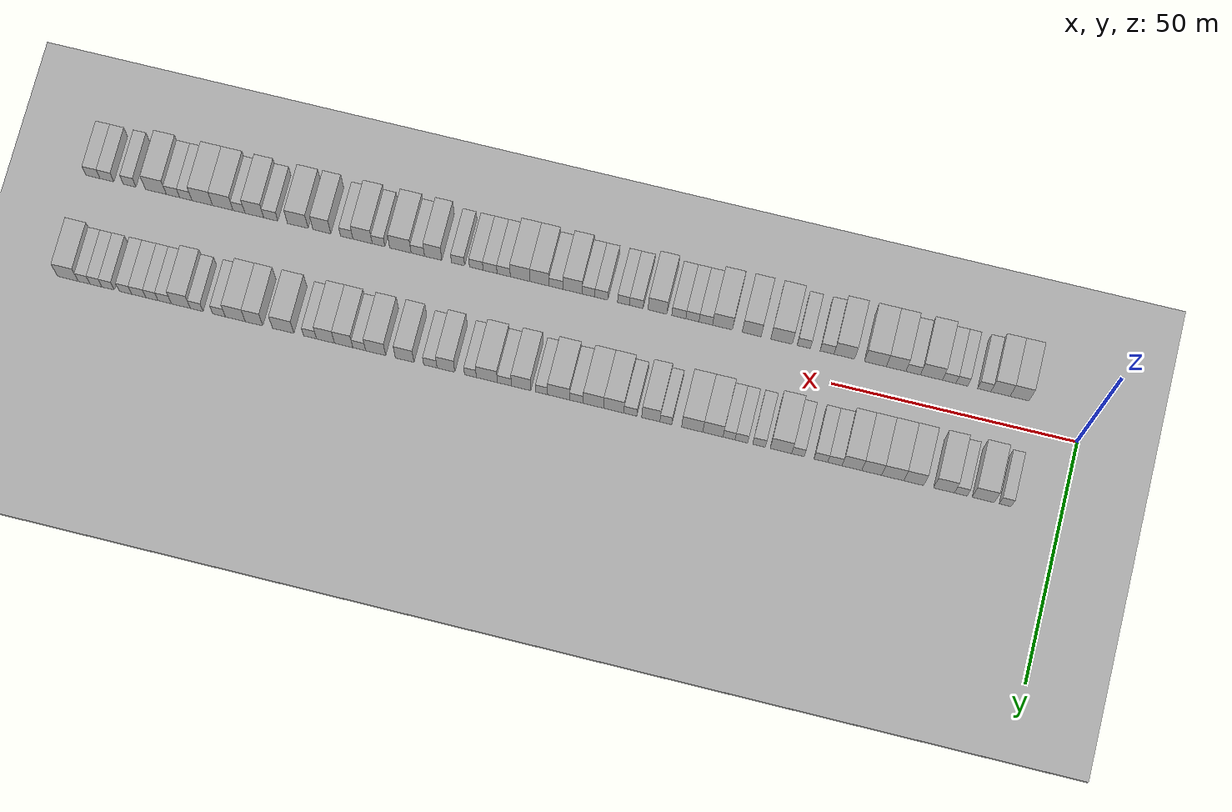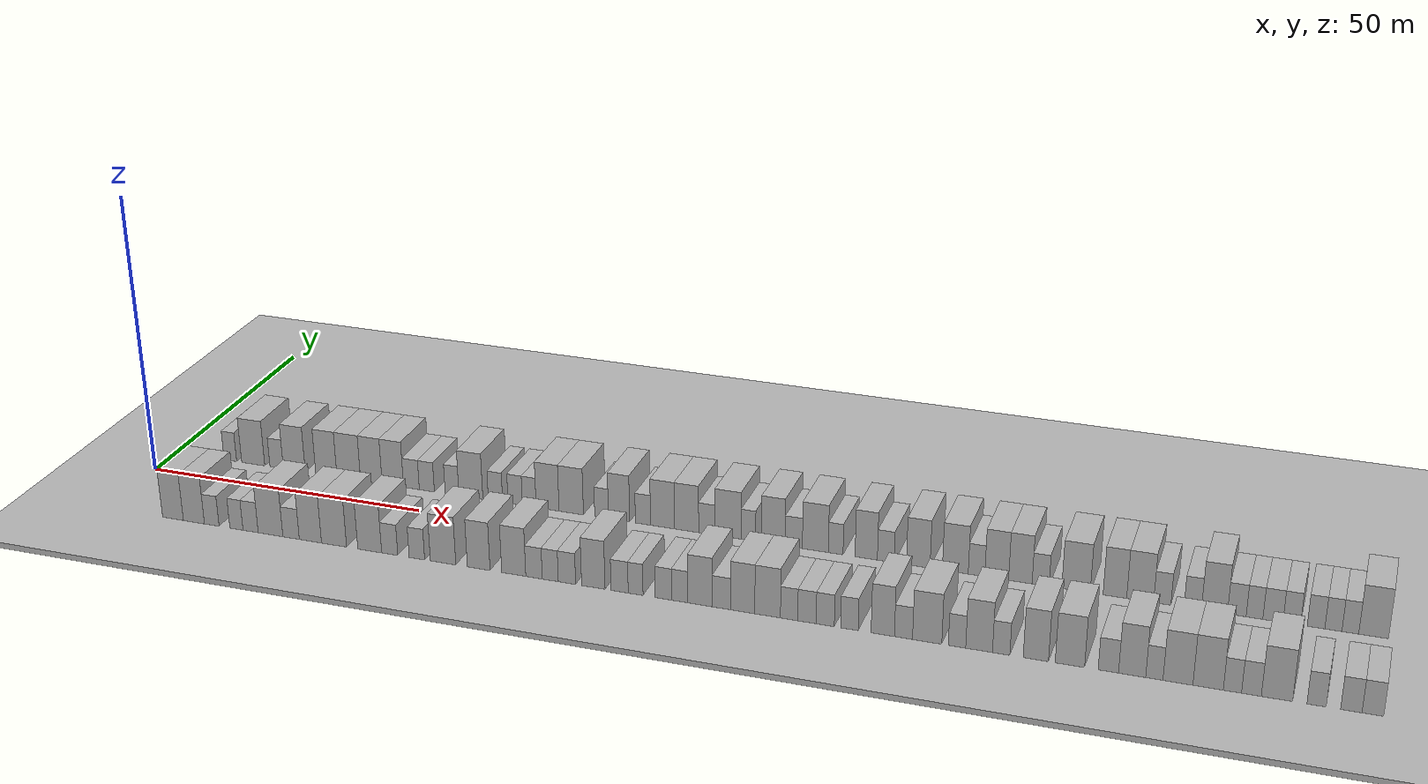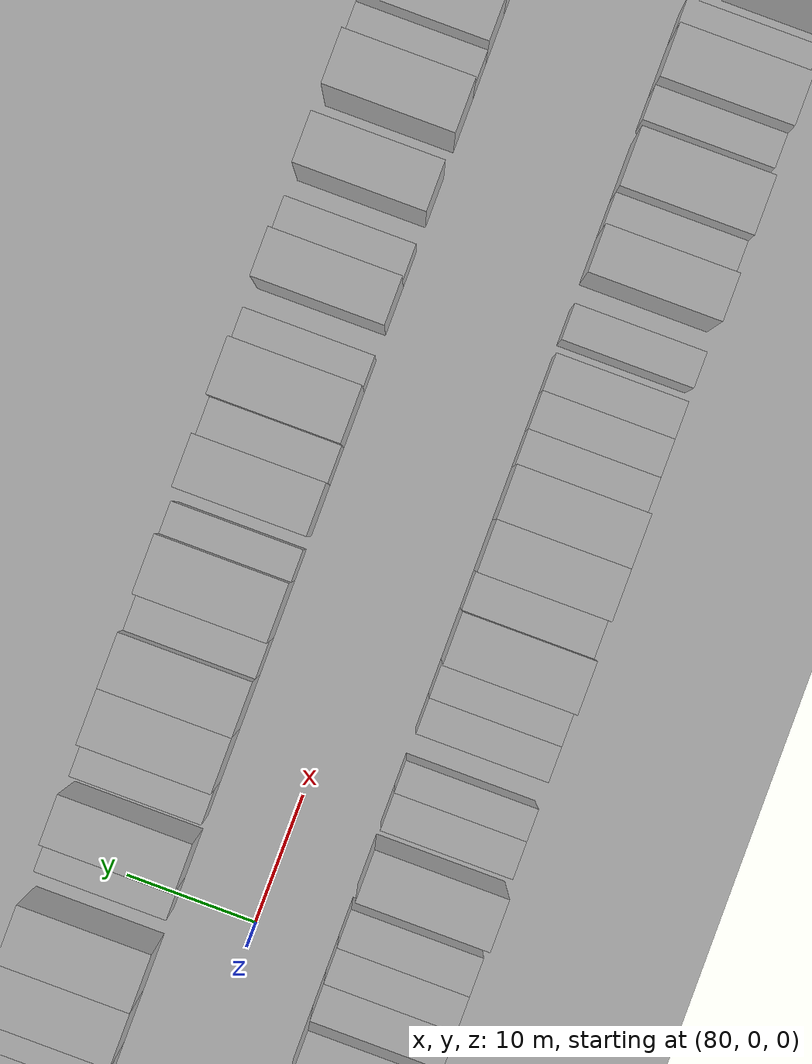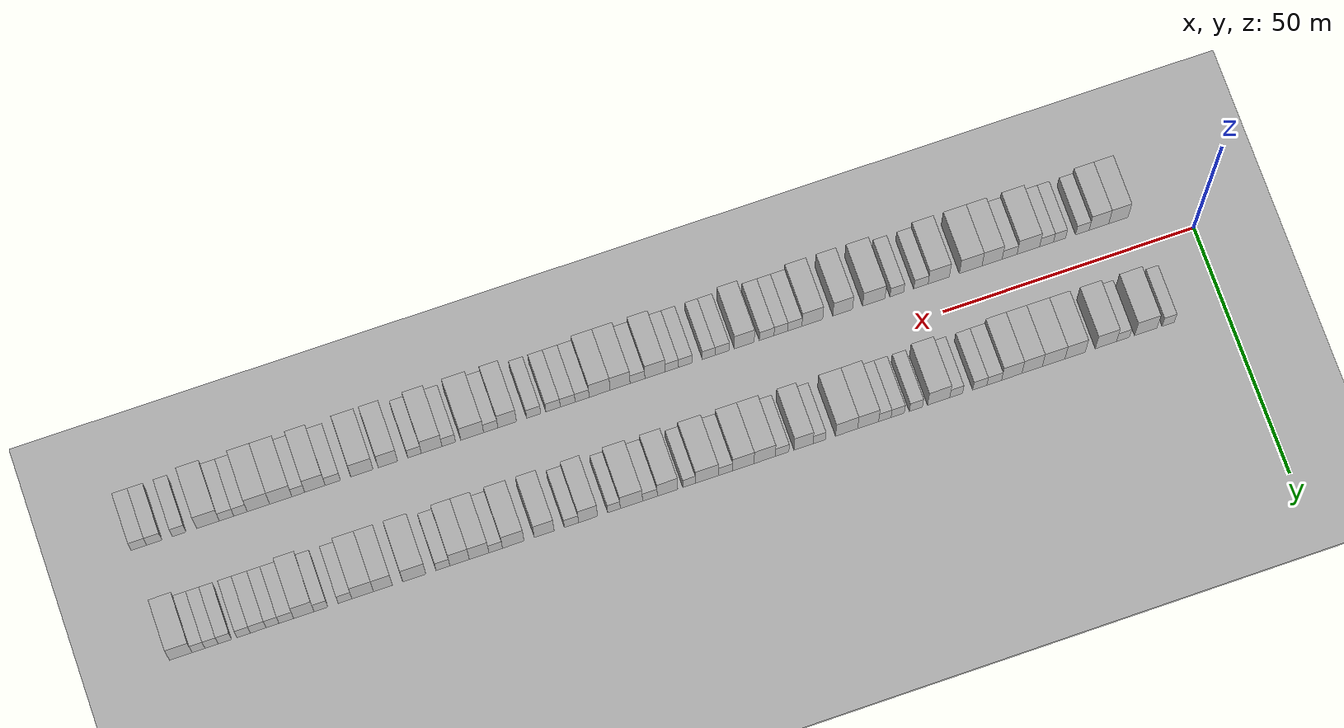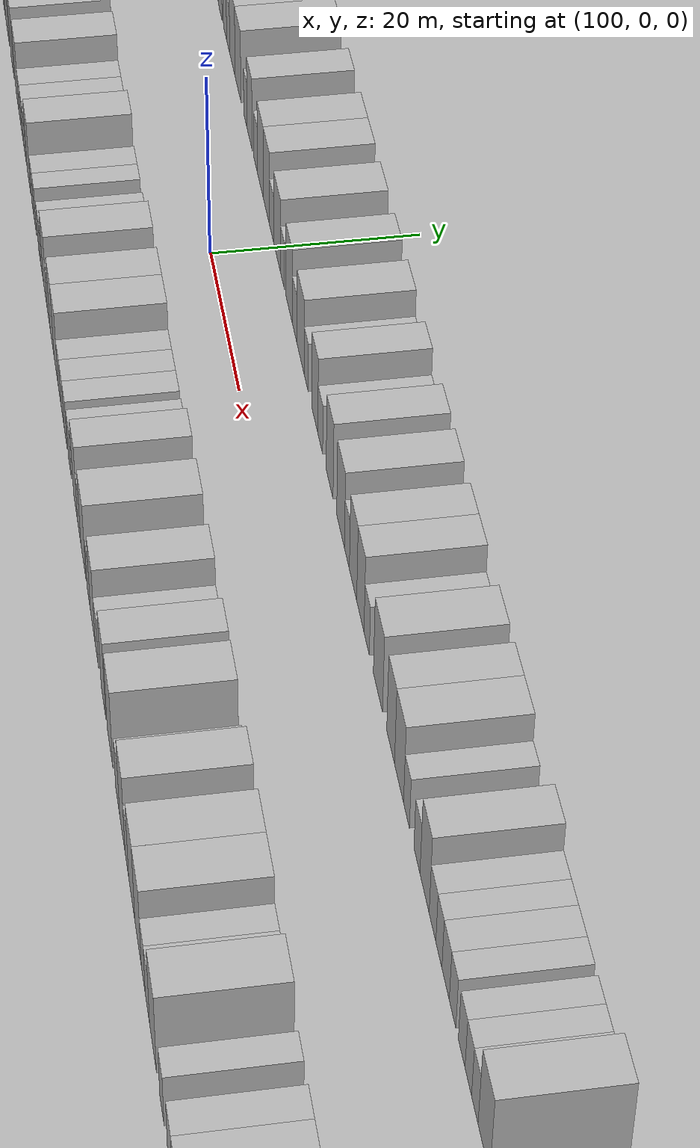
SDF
<?xml version="1.0" encoding="utf-8"?>

<sdf version="1.6">

   <world name="default">

      <gui fullscreen="0">

         <camera name="user_camera">

            <pose>-15 0 4.57585 0 0 0</pose>

            <view_controller>orbit</view_controller>

         </camera>

      </gui>

      <scene>

         <sky>

           <clouds>

             <speed>12</speed>

           </clouds>

         </sky>

         <ambient>0.4 0.4 0.4 1</ambient>

         <background>0.7 0.7 0.7 1</background>

         <shadows>1</shadows>

      </scene>

      <gravity>0 0 -9.8066</gravity>

      <magnetic_field>6e-06 2.3e-05 -4.2e-05</magnetic_field>

      <physics default="0" name="default_physics" type="ode">

         <ode>

            <solver>

               <type>quick</type>

               <iters>10</iters>

               <sor>1.0</sor>

               <use_dynamic_moi_rescaling>0</use_dynamic_moi_rescaling>

            </solver>

            <constraints>

               <cfm>0</cfm>

               <erp>0.2</erp>

               <contact_max_correcting_vel>100</contact_max_correcting_vel>

               <contact_surface_layer>0.001</contact_surface_layer>

            </constraints>

         </ode>

         <max_step_size>0.004</max_step_size>

         <real_time_factor>1</real_time_factor>

         <real_time_update_rate>250</real_time_update_rate>

      </physics>

      <light name="sun" type="directional">

         <cast_shadows>1</cast_shadows>

         <pose>0 0 10 0 0 0</pose>

         <diffuse>0.8 0.8 0.8 1</diffuse>

         <specular>0.2 0.2 0.2 1</specular>

         <attenuation>

            <range>1000</range>

            <constant>0.9</constant>

            <linear>0.01</linear>

            <quadratic>0.001</quadratic>

         </attenuation>

         <direction>-0.5 0.1 -0.9</direction>

      </light>

      <include>

         <name>ground_plane_1</name>

         <uri>model://HANNAS_ground_plane</uri>

         <pose>0 0 0  0 0 0</pose>

      </include>

      <include>

         <name>ground_plane_2</name>

         <uri>model://HANNAS_ground_plane</uri>

         <pose>100 0 0  0 0 0</pose>

      </include>

      <model name="building_1">

         <static>1</static>

         <pose frame="">11.2212 11.0000 0 0.000000 0.000000 1.570796</pose>

         <link name="link">

            <pose frame="">0 0 3.00 0 0 0</pose>

            <collision name="collision">

               <geometry>

                  <box>

                     <size>10.0000 2.4425 6.0000</size>

                  </box>

               </geometry>

               <max_contacts>10</max_contacts>

               <surface>

                  <contact>

                     <ode/>

                  </contact>

                  <bounce/>

                  <friction>

                     <torsional>

                        <ode/>

                     </torsional>

                     <ode/>

                  </friction>

               </surface>

            </collision>

            <visual name="visual">

               <cast_shadows>0</cast_shadows>

               <geometry>

                  <box>

                     <size>10.0000 2.4425 6.0000</size>

                  </box>

               </geometry>

               <material>

                  <script>

                     <uri>model://HANNAS_wall/materials/scripts</uri>

                     <uri>model://HANNAS_wall/materials/textures</uri>

                     <name>vrc/HANNAS_wall</name>

                  </script>

               </material>

            </visual>

            <self_collide>0</self_collide>

            <enable_wind>0</enable_wind>

            <kinematic>0</kinematic>

         </link>

      </model>

      <model name="building_2">

         <static>1</static>

         <pose frame="">15.6833 11.0000 0 0.000000 0.000000 1.570796</pose>

         <link name="link">

            <pose frame="">0 0 4.50 0 0 0</pose>

            <collision name="collision">

               <geometry>

                  <box>

                     <size>10.0000 4.4816 9.0000</size>

                  </box>

               </geometry>

               <max_contacts>10</max_contacts>

               <surface>

                  <contact>

                     <ode/>

                  </contact>

                  <bounce/>

                  <friction>

                     <torsional>

                        <ode/>

                     </torsional>

                     <ode/>

                  </friction>

               </surface>

            </collision>

            <visual name="visual">

               <cast_shadows>0</cast_shadows>

               <geometry>

                  <box>

                     <size>10.0000 4.4816 9.0000</size>

                  </box>

               </geometry>

               <material>

                  <script>

                     <uri>model://HANNAS_wall/materials/scripts</uri>

                     <uri>model://HANNAS_wall/materials/textures</uri>

                     <name>vrc/HANNAS_wall</name>

                  </script>

               </material>

            </visual>

            <self_collide>0</self_collide>

            <enable_wind>0</enable_wind>

            <kinematic>0</kinematic>

         </link>

      </model>

      <model name="building_3">

         <static>1</static>

         <pose frame="">20.2165 11.0000 0 0.000000 0.000000 1.570796</pose>

         <link name="link">

            <pose frame="">0 0 3.00 0 0 0</pose>

            <collision name="collision">

               <geometry>

                  <box>

                     <size>10.0000 2.5849 6.0000</size>

                  </box>

               </geometry>

               <max_contacts>10</max_contacts>

               <surface>

                  <contact>

                     <ode/>

                  </contact>

                  <bounce/>

                  <friction>

                     <torsional>

                        <ode/>

                     </torsional>

                     <ode/>

                  </friction>

               </surface>

            </collision>

            <visual name="visual">

               <cast_shadows>0</cast_shadows>

               <geometry>

                  <box>

                     <size>10.0000 2.5849 6.0000</size>

                  </box>

               </geometry>

               <material>

                  <script>

                     <uri>model://HANNAS_wall/materials/scripts</uri>

                     <uri>model://HANNAS_wall/materials/textures</uri>

                     <name>vrc/HANNAS_wall</name>

                  </script>

               </material>

            </visual>

            <self_collide>0</self_collide>

            <enable_wind>0</enable_wind>

            <kinematic>0</kinematic>

         </link>

      </model>

      <model name="building_4">

         <static>1</static>

         <pose frame="">23.6177 11.0000 0 0.000000 0.000000 1.570796</pose>

         <link name="link">

            <pose frame="">0 0 4.50 0 0 0</pose>

            <collision name="collision">

               <geometry>

                  <box>

                     <size>10.0000 4.2175 9.0000</size>

                  </box>

               </geometry>

               <max_contacts>10</max_contacts>

               <surface>

                  <contact>

                     <ode/>

                  </contact>

                  <bounce/>

                  <friction>

                     <torsional>

                        <ode/>

                     </torsional>

                     <ode/>

                  </friction>

               </surface>

            </collision>

            <visual name="visual">

               <cast_shadows>0</cast_shadows>

               <geometry>

                  <box>

                     <size>10.0000 4.2175 9.0000</size>

                  </box>

               </geometry>

               <material>

                  <script>

                     <uri>model://HANNAS_wall/materials/scripts</uri>

                     <uri>model://HANNAS_wall/materials/textures</uri>

                     <name>vrc/HANNAS_wall</name>

                  </script>

               </material>

            </visual>

            <self_collide>0</self_collide>

            <enable_wind>0</enable_wind>

            <kinematic>0</kinematic>

         </link>

      </model>

      <model name="building_5">

         <static>1</static>

         <pose frame="">29.7440 11.0000 0 0.000000 0.000000 1.570796</pose>

         <link name="link">

            <pose frame="">0 0 4.50 0 0 0</pose>

            <collision name="collision">

               <geometry>

                  <box>

                     <size>10.0000 4.0352 9.0000</size>

                  </box>

               </geometry>

               <max_contacts>10</max_contacts>

               <surface>

                  <contact>

                     <ode/>

                  </contact>

                  <bounce/>

                  <friction>

                     <torsional>

                        <ode/>

                     </torsional>

                     <ode/>

                  </friction>

               </surface>

            </collision>

            <visual name="visual">

               <cast_shadows>0</cast_shadows>

               <geometry>

                  <box>

                     <size>10.0000 4.0352 9.0000</size>

                  </box>

               </geometry>

               <material>

                  <script>

                     <uri>model://HANNAS_wall/materials/scripts</uri>

                     <uri>model://HANNAS_wall/materials/textures</uri>

                     <name>vrc/HANNAS_wall</name>

                  </script>

               </material>

            </visual>

            <self_collide>0</self_collide>

            <enable_wind>0</enable_wind>

            <kinematic>0</kinematic>

         </link>

      </model>

      <model name="building_6">

         <static>1</static>

         <pose frame="">34.0001 11.0000 0 0.000000 0.000000 1.570796</pose>

         <link name="link">

            <pose frame="">0 0 4.50 0 0 0</pose>

            <collision name="collision">

               <geometry>

                  <box>

                     <size>10.0000 4.4770 9.0000</size>

                  </box>

               </geometry>

               <max_contacts>10</max_contacts>

               <surface>

                  <contact>

                     <ode/>

                  </contact>

                  <bounce/>

                  <friction>

                     <torsional>

                        <ode/>

                     </torsional>

                     <ode/>

                  </friction>

               </surface>

            </collision>

            <visual name="visual">

               <cast_shadows>0</cast_shadows>

               <geometry>

                  <box>

                     <size>10.0000 4.4770 9.0000</size>

                  </box>

               </geometry>

               <material>

                  <script>

                     <uri>model://HANNAS_wall/materials/scripts</uri>

                     <uri>model://HANNAS_wall/materials/textures</uri>

                     <name>vrc/HANNAS_wall</name>

                  </script>

               </material>

            </visual>

            <self_collide>0</self_collide>

            <enable_wind>0</enable_wind>

            <kinematic>0</kinematic>

         </link>

      </model>

      <model name="building_7">

         <static>1</static>

         <pose frame="">38.2673 11.0000 0 0.000000 0.000000 1.570796</pose>

         <link name="link">

            <pose frame="">0 0 4.50 0 0 0</pose>

            <collision name="collision">

               <geometry>

                  <box>

                     <size>10.0000 4.0575 9.0000</size>

                  </box>

               </geometry>

               <max_contacts>10</max_contacts>

               <surface>

                  <contact>

                     <ode/>

                  </contact>

                  <bounce/>

                  <friction>

                     <torsional>

                        <ode/>

                     </torsional>

                     <ode/>

                  </friction>

               </surface>

            </collision>

            <visual name="visual">

               <cast_shadows>0</cast_shadows>

               <geometry>

                  <box>

                     <size>10.0000 4.0575 9.0000</size>

                  </box>

               </geometry>

               <material>

                  <script>

                     <uri>model://HANNAS_wall/materials/scripts</uri>

                     <uri>model://HANNAS_wall/materials/textures</uri>

                     <name>vrc/HANNAS_wall</name>

                  </script>

               </material>

            </visual>

            <self_collide>0</self_collide>

            <enable_wind>0</enable_wind>

            <kinematic>0</kinematic>

         </link>

      </model>

      <model name="building_8">

         <static>1</static>

         <pose frame="">42.3002 11.0000 0 0.000000 0.000000 1.570796</pose>

         <link name="link">

            <pose frame="">0 0 4.50 0 0 0</pose>

            <collision name="collision">

               <geometry>

                  <box>

                     <size>10.0000 4.0082 9.0000</size>

                  </box>

               </geometry>

               <max_contacts>10</max_contacts>

               <surface>

                  <contact>

                     <ode/>

                  </contact>

                  <bounce/>

                  <friction>

                     <torsional>

                        <ode/>

                     </torsional>

                     <ode/>

                  </friction>

               </surface>

            </collision>

            <visual name="visual">

               <cast_shadows>0</cast_shadows>

               <geometry>

                  <box>

                     <size>10.0000 4.0082 9.0000</size>

                  </box>

               </geometry>

               <material>

                  <script>

                     <uri>model://HANNAS_wall/materials/scripts</uri>

                     <uri>model://HANNAS_wall/materials/textures</uri>

                     <name>vrc/HANNAS_wall</name>

                  </script>

               </material>

            </visual>

            <self_collide>0</self_collide>

            <enable_wind>0</enable_wind>

            <kinematic>0</kinematic>

         </link>

      </model>

      <model name="building_9">

         <static>1</static>

         <pose frame="">45.7667 11.0000 0 0.000000 0.000000 1.570796</pose>

         <link name="link">

            <pose frame="">0 0 3.00 0 0 0</pose>

            <collision name="collision">

               <geometry>

                  <box>

                     <size>10.0000 2.9247 6.0000</size>

                  </box>

               </geometry>

               <max_contacts>10</max_contacts>

               <surface>

                  <contact>

                     <ode/>

                  </contact>

                  <bounce/>

                  <friction>

                     <torsional>

                        <ode/>

                     </torsional>

                     <ode/>

                  </friction>

               </surface>

            </collision>

            <visual name="visual">

               <cast_shadows>0</cast_shadows>

               <geometry>

                  <box>

                     <size>10.0000 2.9247 6.0000</size>

                  </box>

               </geometry>

               <material>

                  <script>

                     <uri>model://HANNAS_wall/materials/scripts</uri>

                     <uri>model://HANNAS_wall/materials/textures</uri>

                     <name>vrc/HANNAS_wall</name>

                  </script>

               </material>

            </visual>

            <self_collide>0</self_collide>

            <enable_wind>0</enable_wind>

            <kinematic>0</kinematic>

         </link>

      </model>

      <model name="building_10">

         <static>1</static>

         <pose frame="">48.6232 11.0000 0 0.000000 0.000000 1.570796</pose>

         <link name="link">

            <pose frame="">0 0 3.00 0 0 0</pose>

            <collision name="collision">

               <geometry>

                  <box>

                     <size>10.0000 2.7884 6.0000</size>

                  </box>

               </geometry>

               <max_contacts>10</max_contacts>

               <surface>

                  <contact>

                     <ode/>

                  </contact>

                  <bounce/>

                  <friction>

                     <torsional>

                        <ode/>

                     </torsional>

                     <ode/>

                  </friction>

               </surface>

            </collision>

            <visual name="visual">

               <cast_shadows>0</cast_shadows>

               <geometry>

                  <box>

                     <size>10.0000 2.7884 6.0000</size>

                  </box>

               </geometry>

               <material>

                  <script>

                     <uri>model://HANNAS_wall/materials/scripts</uri>

                     <uri>model://HANNAS_wall/materials/textures</uri>

                     <name>vrc/HANNAS_wall</name>

                  </script>

               </material>

            </visual>

            <self_collide>0</self_collide>

            <enable_wind>0</enable_wind>

            <kinematic>0</kinematic>

         </link>

      </model>

      <model name="building_11">

         <static>1</static>

         <pose frame="">53.2833 11.0000 0 0.000000 0.000000 1.570796</pose>

         <link name="link">

            <pose frame="">0 0 3.00 0 0 0</pose>

            <collision name="collision">

               <geometry>

                  <box>

                     <size>10.0000 2.5317 6.0000</size>

                  </box>

               </geometry>

               <max_contacts>10</max_contacts>

               <surface>

                  <contact>

                     <ode/>

                  </contact>

                  <bounce/>

                  <friction>

                     <torsional>

                        <ode/>

                     </torsional>

                     <ode/>

                  </friction>

               </surface>

            </collision>

            <visual name="visual">

               <cast_shadows>0</cast_shadows>

               <geometry>

                  <box>

                     <size>10.0000 2.5317 6.0000</size>

                  </box>

               </geometry>

               <material>

                  <script>

                     <uri>model://HANNAS_wall/materials/scripts</uri>

                     <uri>model://HANNAS_wall/materials/textures</uri>

                     <name>vrc/HANNAS_wall</name>

                  </script>

               </material>

            </visual>

            <self_collide>0</self_collide>

            <enable_wind>0</enable_wind>

            <kinematic>0</kinematic>

         </link>

      </model>

      <model name="building_12">

         <static>1</static>

         <pose frame="">56.7394 11.0000 0 0.000000 0.000000 1.570796</pose>

         <link name="link">

            <pose frame="">0 0 4.50 0 0 0</pose>

            <collision name="collision">

               <geometry>

                  <box>

                     <size>10.0000 4.3805 9.0000</size>

                  </box>

               </geometry>

               <max_contacts>10</max_contacts>

               <surface>

                  <contact>

                     <ode/>

                  </contact>

                  <bounce/>

                  <friction>

                     <torsional>

                        <ode/>

                     </torsional>

                     <ode/>

                  </friction>

               </surface>

            </collision>

            <visual name="visual">

               <cast_shadows>0</cast_shadows>

               <geometry>

                  <box>

                     <size>10.0000 4.3805 9.0000</size>

                  </box>

               </geometry>

               <material>

                  <script>

                     <uri>model://HANNAS_wall/materials/scripts</uri>

                     <uri>model://HANNAS_wall/materials/textures</uri>

                     <name>vrc/HANNAS_wall</name>

                  </script>

               </material>

            </visual>

            <self_collide>0</self_collide>

            <enable_wind>0</enable_wind>

            <kinematic>0</kinematic>

         </link>

      </model>

      <model name="building_13">

         <static>1</static>

         <pose frame="">61.2261 11.0000 0 0.000000 0.000000 1.570796</pose>

         <link name="link">

            <pose frame="">0 0 3.00 0 0 0</pose>

            <collision name="collision">

               <geometry>

                  <box>

                     <size>10.0000 2.5931 6.0000</size>

                  </box>

               </geometry>

               <max_contacts>10</max_contacts>

               <surface>

                  <contact>

                     <ode/>

                  </contact>

                  <bounce/>

                  <friction>

                     <torsional>

                        <ode/>

                     </torsional>

                     <ode/>

                  </friction>

               </surface>

            </collision>

            <visual name="visual">

               <cast_shadows>0</cast_shadows>

               <geometry>

                  <box>

                     <size>10.0000 2.5931 6.0000</size>

                  </box>

               </geometry>

               <material>

                  <script>

                     <uri>model://HANNAS_wall/materials/scripts</uri>

                     <uri>model://HANNAS_wall/materials/textures</uri>

                     <name>vrc/HANNAS_wall</name>

                  </script>

               </material>

            </visual>

            <self_collide>0</self_collide>

            <enable_wind>0</enable_wind>

            <kinematic>0</kinematic>

         </link>

      </model>

      <model name="building_14">

         <static>1</static>

         <pose frame="">64.8206 11.0000 0 0.000000 0.000000 1.570796</pose>

         <link name="link">

            <pose frame="">0 0 3.00 0 0 0</pose>

            <collision name="collision">

               <geometry>

                  <box>

                     <size>10.0000 2.5959 6.0000</size>

                  </box>

               </geometry>

               <max_contacts>10</max_contacts>

               <surface>

                  <contact>

                     <ode/>

                  </contact>

                  <bounce/>

                  <friction>

                     <torsional>

                        <ode/>

                     </torsional>

                     <ode/>

                  </friction>

               </surface>

            </collision>

            <visual name="visual">

               <cast_shadows>0</cast_shadows>

               <geometry>

                  <box>

                     <size>10.0000 2.5959 6.0000</size>

                  </box>

               </geometry>

               <material>

                  <script>

                     <uri>model://HANNAS_wall/materials/scripts</uri>

                     <uri>model://HANNAS_wall/materials/textures</uri>

                     <name>vrc/HANNAS_wall</name>

                  </script>

               </material>

            </visual>

            <self_collide>0</self_collide>

            <enable_wind>0</enable_wind>

            <kinematic>0</kinematic>

         </link>

      </model>

      <model name="building_15">

         <static>1</static>

         <pose frame="">67.3522 11.0000 0 0.000000 0.000000 1.570796</pose>

         <link name="link">

            <pose frame="">0 0 3.00 0 0 0</pose>

            <collision name="collision">

               <geometry>

                  <box>

                     <size>10.0000 2.4673 6.0000</size>

                  </box>

               </geometry>

               <max_contacts>10</max_contacts>

               <surface>

                  <contact>

                     <ode/>

                  </contact>

                  <bounce/>

                  <friction>

                     <torsional>

                        <ode/>

                     </torsional>

                     <ode/>

                  </friction>

               </surface>

            </collision>

            <visual name="visual">

               <cast_shadows>0</cast_shadows>

               <geometry>

                  <box>

                     <size>10.0000 2.4673 6.0000</size>

                  </box>

               </geometry>

               <material>

                  <script>

                     <uri>model://HANNAS_wall/materials/scripts</uri>

                     <uri>model://HANNAS_wall/materials/textures</uri>

                     <name>vrc/HANNAS_wall</name>

                  </script>

               </material>

            </visual>

            <self_collide>0</self_collide>

            <enable_wind>0</enable_wind>

            <kinematic>0</kinematic>

         </link>

      </model>

      <model name="building_16">

         <static>1</static>

         <pose frame="">70.6427 11.0000 0 0.000000 0.000000 1.570796</pose>

         <link name="link">

            <pose frame="">0 0 4.50 0 0 0</pose>

            <collision name="collision">

               <geometry>

                  <box>

                     <size>10.0000 4.1138 9.0000</size>

                  </box>

               </geometry>

               <max_contacts>10</max_contacts>

               <surface>

                  <contact>

                     <ode/>

                  </contact>

                  <bounce/>

                  <friction>

                     <torsional>

                        <ode/>

                     </torsional>

                     <ode/>

                  </friction>

               </surface>

            </collision>

            <visual name="visual">

               <cast_shadows>0</cast_shadows>

               <geometry>

                  <box>

                     <size>10.0000 4.1138 9.0000</size>

                  </box>

               </geometry>

               <material>

                  <script>

                     <uri>model://HANNAS_wall/materials/scripts</uri>

                     <uri>model://HANNAS_wall/materials/textures</uri>

                     <name>vrc/HANNAS_wall</name>

                  </script>

               </material>

            </visual>

            <self_collide>0</self_collide>

            <enable_wind>0</enable_wind>

            <kinematic>0</kinematic>

         </link>

      </model>

      <model name="building_17">

         <static>1</static>

         <pose frame="">74.8730 11.0000 0 0.000000 0.000000 1.570796</pose>

         <link name="link">

            <pose frame="">0 0 4.50 0 0 0</pose>

            <collision name="collision">

               <geometry>

                  <box>

                     <size>10.0000 4.3467 9.0000</size>

                  </box>

               </geometry>

               <max_contacts>10</max_contacts>

               <surface>

                  <contact>

                     <ode/>

                  </contact>

                  <bounce/>

                  <friction>

                     <torsional>

                        <ode/>

                     </torsional>

                     <ode/>

                  </friction>

               </surface>

            </collision>

            <visual name="visual">

               <cast_shadows>0</cast_shadows>

               <geometry>

                  <box>

                     <size>10.0000 4.3467 9.0000</size>

                  </box>

               </geometry>

               <material>

                  <script>

                     <uri>model://HANNAS_wall/materials/scripts</uri>

                     <uri>model://HANNAS_wall/materials/textures</uri>

                     <name>vrc/HANNAS_wall</name>

                  </script>

               </material>

            </visual>

            <self_collide>0</self_collide>

            <enable_wind>0</enable_wind>

            <kinematic>0</kinematic>

         </link>

      </model>

      <model name="building_18">

         <static>1</static>

         <pose frame="">80.2642 11.0000 0 0.000000 0.000000 1.570796</pose>

         <link name="link">

            <pose frame="">0 0 3.00 0 0 0</pose>

            <collision name="collision">

               <geometry>

                  <box>

                     <size>10.0000 2.4358 6.0000</size>

                  </box>

               </geometry>

               <max_contacts>10</max_contacts>

               <surface>

                  <contact>

                     <ode/>

                  </contact>

                  <bounce/>

                  <friction>

                     <torsional>

                        <ode/>

                     </torsional>

                     <ode/>

                  </friction>

               </surface>

            </collision>

            <visual name="visual">

               <cast_shadows>0</cast_shadows>

               <geometry>

                  <box>

                     <size>10.0000 2.4358 6.0000</size>

                  </box>

               </geometry>

               <material>

                  <script>

                     <uri>model://HANNAS_wall/materials/scripts</uri>

                     <uri>model://HANNAS_wall/materials/textures</uri>

                     <name>vrc/HANNAS_wall</name>

                  </script>

               </material>

            </visual>

            <self_collide>0</self_collide>

            <enable_wind>0</enable_wind>

            <kinematic>0</kinematic>

         </link>

      </model>

      <model name="building_19">

         <static>1</static>

         <pose frame="">83.3483 11.0000 0 0.000000 0.000000 1.570796</pose>

         <link name="link">

            <pose frame="">0 0 4.50 0 0 0</pose>

            <collision name="collision">

               <geometry>

                  <box>

                     <size>10.0000 3.7323 9.0000</size>

                  </box>

               </geometry>

               <max_contacts>10</max_contacts>

               <surface>

                  <contact>

                     <ode/>

                  </contact>

                  <bounce/>

                  <friction>

                     <torsional>

                        <ode/>

                     </torsional>

                     <ode/>

                  </friction>

               </surface>

            </collision>

            <visual name="visual">

               <cast_shadows>0</cast_shadows>

               <geometry>

                  <box>

                     <size>10.0000 3.7323 9.0000</size>

                  </box>

               </geometry>

               <material>

                  <script>

                     <uri>model://HANNAS_wall/materials/scripts</uri>

                     <uri>model://HANNAS_wall/materials/textures</uri>

                     <name>vrc/HANNAS_wall</name>

                  </script>

               </material>

            </visual>

            <self_collide>0</self_collide>

            <enable_wind>0</enable_wind>

            <kinematic>0</kinematic>

         </link>

      </model>

      <model name="building_20">

         <static>1</static>

         <pose frame="">87.5436 11.0000 0 0.000000 0.000000 1.570796</pose>

         <link name="link">

            <pose frame="">0 0 3.00 0 0 0</pose>

            <collision name="collision">

               <geometry>

                  <box>

                     <size>10.0000 2.6584 6.0000</size>

                  </box>

               </geometry>

               <max_contacts>10</max_contacts>

               <surface>

                  <contact>

                     <ode/>

                  </contact>

                  <bounce/>

                  <friction>

                     <torsional>

                        <ode/>

                     </torsional>

                     <ode/>

                  </friction>

               </surface>

            </collision>

            <visual name="visual">

               <cast_shadows>0</cast_shadows>

               <geometry>

                  <box>

                     <size>10.0000 2.6584 6.0000</size>

                  </box>

               </geometry>

               <material>

                  <script>

                     <uri>model://HANNAS_wall/materials/scripts</uri>

                     <uri>model://HANNAS_wall/materials/textures</uri>

                     <name>vrc/HANNAS_wall</name>

                  </script>

               </material>

            </visual>

            <self_collide>0</self_collide>

            <enable_wind>0</enable_wind>

            <kinematic>0</kinematic>

         </link>

      </model>

      <model name="building_21">

         <static>1</static>

         <pose frame="">90.9556 11.0000 0 0.000000 0.000000 1.570796</pose>

         <link name="link">

            <pose frame="">0 0 4.50 0 0 0</pose>

            <collision name="collision">

               <geometry>

                  <box>

                     <size>10.0000 4.1655 9.0000</size>

                  </box>

               </geometry>

               <max_contacts>10</max_contacts>

               <surface>

                  <contact>

                     <ode/>

                  </contact>

                  <bounce/>

                  <friction>

                     <torsional>

                        <ode/>

                     </torsional>

                     <ode/>

                  </friction>

               </surface>

            </collision>

            <visual name="visual">

               <cast_shadows>0</cast_shadows>

               <geometry>

                  <box>

                     <size>10.0000 4.1655 9.0000</size>

                  </box>

               </geometry>

               <material>

                  <script>

                     <uri>model://HANNAS_wall/materials/scripts</uri>

                     <uri>model://HANNAS_wall/materials/textures</uri>

                     <name>vrc/HANNAS_wall</name>

                  </script>

               </material>

            </visual>

            <self_collide>0</self_collide>

            <enable_wind>0</enable_wind>

            <kinematic>0</kinematic>

         </link>

      </model>

      <model name="building_22">

         <static>1</static>

         <pose frame="">95.1269 11.0000 0 0.000000 0.000000 1.570796</pose>

         <link name="link">

            <pose frame="">0 0 4.50 0 0 0</pose>

            <collision name="collision">

               <geometry>

                  <box>

                     <size>10.0000 4.1772 9.0000</size>

                  </box>

               </geometry>

               <max_contacts>10</max_contacts>

               <surface>

                  <contact>

                     <ode/>

                  </contact>

                  <bounce/>

                  <friction>

                     <torsional>

                        <ode/>

                     </torsional>

                     <ode/>

                  </friction>

               </surface>

            </collision>

            <visual name="visual">

               <cast_shadows>0</cast_shadows>

               <geometry>

                  <box>

                     <size>10.0000 4.1772 9.0000</size>

                  </box>

               </geometry>

               <material>

                  <script>

                     <uri>model://HANNAS_wall/materials/scripts</uri>

                     <uri>model://HANNAS_wall/materials/textures</uri>

                     <name>vrc/HANNAS_wall</name>

                  </script>

               </material>

            </visual>

            <self_collide>0</self_collide>

            <enable_wind>0</enable_wind>

            <kinematic>0</kinematic>

         </link>

      </model>

      <model name="building_23">

         <static>1</static>

         <pose frame="">98.6332 11.0000 0 0.000000 0.000000 1.570796</pose>

         <link name="link">

            <pose frame="">0 0 3.00 0 0 0</pose>

            <collision name="collision">

               <geometry>

                  <box>

                     <size>10.0000 2.8355 6.0000</size>

                  </box>

               </geometry>

               <max_contacts>10</max_contacts>

               <surface>

                  <contact>

                     <ode/>

                  </contact>

                  <bounce/>

                  <friction>

                     <torsional>

                        <ode/>

                     </torsional>

                     <ode/>

                  </friction>

               </surface>

            </collision>

            <visual name="visual">

               <cast_shadows>0</cast_shadows>

               <geometry>

                  <box>

                     <size>10.0000 2.8355 6.0000</size>

                  </box>

               </geometry>

               <material>

                  <script>

                     <uri>model://HANNAS_wall/materials/scripts</uri>

                     <uri>model://HANNAS_wall/materials/textures</uri>

                     <name>vrc/HANNAS_wall</name>

                  </script>

               </material>

            </visual>

            <self_collide>0</self_collide>

            <enable_wind>0</enable_wind>

            <kinematic>0</kinematic>

         </link>

      </model>

      <model name="building_24">

         <static>1</static>

         <pose frame="">102.2851 11.0000 0 0.000000 0.000000 1.570796</pose>

         <link name="link">

            <pose frame="">0 0 4.50 0 0 0</pose>

            <collision name="collision">

               <geometry>

                  <box>

                     <size>10.0000 4.4683 9.0000</size>

                  </box>

               </geometry>

               <max_contacts>10</max_contacts>

               <surface>

                  <contact>

                     <ode/>

                  </contact>

                  <bounce/>

                  <friction>

                     <torsional>

                        <ode/>

                     </torsional>

                     <ode/>

                  </friction>

               </surface>

            </collision>

            <visual name="visual">

               <cast_shadows>0</cast_shadows>

               <geometry>

                  <box>

                     <size>10.0000 4.4683 9.0000</size>

                  </box>

               </geometry>

               <material>

                  <script>

                     <uri>model://HANNAS_wall/materials/scripts</uri>

                     <uri>model://HANNAS_wall/materials/textures</uri>

                     <name>vrc/HANNAS_wall</name>

                  </script>

               </material>

            </visual>

            <self_collide>0</self_collide>

            <enable_wind>0</enable_wind>

            <kinematic>0</kinematic>

         </link>

      </model>

      <model name="building_25">

         <static>1</static>

         <pose frame="">105.7495 11.0000 0 0.000000 0.000000 1.570796</pose>

         <link name="link">

            <pose frame="">0 0 3.00 0 0 0</pose>

            <collision name="collision">

               <geometry>

                  <box>

                     <size>10.0000 2.4605 6.0000</size>

                  </box>

               </geometry>

               <max_contacts>10</max_contacts>

               <surface>

                  <contact>

                     <ode/>

                  </contact>

                  <bounce/>

                  <friction>

                     <torsional>

                        <ode/>

                     </torsional>

                     <ode/>

                  </friction>

               </surface>

            </collision>

            <visual name="visual">

               <cast_shadows>0</cast_shadows>

               <geometry>

                  <box>

                     <size>10.0000 2.4605 6.0000</size>

                  </box>

               </geometry>

               <material>

                  <script>

                     <uri>model://HANNAS_wall/materials/scripts</uri>

                     <uri>model://HANNAS_wall/materials/textures</uri>

                     <name>vrc/HANNAS_wall</name>

                  </script>

               </material>

            </visual>

            <self_collide>0</self_collide>

            <enable_wind>0</enable_wind>

            <kinematic>0</kinematic>

         </link>

      </model>

      <model name="building_26">

         <static>1</static>

         <pose frame="">109.9729 11.0000 0 0.000000 0.000000 1.570796</pose>

         <link name="link">

            <pose frame="">0 0 4.50 0 0 0</pose>

            <collision name="collision">

               <geometry>

                  <box>

                     <size>10.0000 3.9864 9.0000</size>

                  </box>

               </geometry>

               <max_contacts>10</max_contacts>

               <surface>

                  <contact>

                     <ode/>

                  </contact>

                  <bounce/>

                  <friction>

                     <torsional>

                        <ode/>

                     </torsional>

                     <ode/>

                  </friction>

               </surface>

            </collision>

            <visual name="visual">

               <cast_shadows>0</cast_shadows>

               <geometry>

                  <box>

                     <size>10.0000 3.9864 9.0000</size>

                  </box>

               </geometry>

               <material>

                  <script>

                     <uri>model://HANNAS_wall/materials/scripts</uri>

                     <uri>model://HANNAS_wall/materials/textures</uri>

                     <name>vrc/HANNAS_wall</name>

                  </script>

               </material>

            </visual>

            <self_collide>0</self_collide>

            <enable_wind>0</enable_wind>

            <kinematic>0</kinematic>

         </link>

      </model>

      <model name="building_27">

         <static>1</static>

         <pose frame="">113.4090 11.0000 0 0.000000 0.000000 1.570796</pose>

         <link name="link">

            <pose frame="">0 0 3.00 0 0 0</pose>

            <collision name="collision">

               <geometry>

                  <box>

                     <size>10.0000 2.8859 6.0000</size>

                  </box>

               </geometry>

               <max_contacts>10</max_contacts>

               <surface>

                  <contact>

                     <ode/>

                  </contact>

                  <bounce/>

                  <friction>

                     <torsional>

                        <ode/>

                     </torsional>

                     <ode/>

                  </friction>

               </surface>

            </collision>

            <visual name="visual">

               <cast_shadows>0</cast_shadows>

               <geometry>

                  <box>

                     <size>10.0000 2.8859 6.0000</size>

                  </box>

               </geometry>

               <material>

                  <script>

                     <uri>model://HANNAS_wall/materials/scripts</uri>

                     <uri>model://HANNAS_wall/materials/textures</uri>

                     <name>vrc/HANNAS_wall</name>

                  </script>

               </material>

            </visual>

            <self_collide>0</self_collide>

            <enable_wind>0</enable_wind>

            <kinematic>0</kinematic>

         </link>

      </model>

      <model name="building_28">

         <static>1</static>

         <pose frame="">117.0233 11.0000 0 0.000000 0.000000 1.570796</pose>

         <link name="link">

            <pose frame="">0 0 4.50 0 0 0</pose>

            <collision name="collision">

               <geometry>

                  <box>

                     <size>10.0000 4.3427 9.0000</size>

                  </box>

               </geometry>

               <max_contacts>10</max_contacts>

               <surface>

                  <contact>

                     <ode/>

                  </contact>

                  <bounce/>

                  <friction>

                     <torsional>

                        <ode/>

                     </torsional>

                     <ode/>

                  </friction>

               </surface>

            </collision>

            <visual name="visual">

               <cast_shadows>0</cast_shadows>

               <geometry>

                  <box>

                     <size>10.0000 4.3427 9.0000</size>

                  </box>

               </geometry>

               <material>

                  <script>

                     <uri>model://HANNAS_wall/materials/scripts</uri>

                     <uri>model://HANNAS_wall/materials/textures</uri>

                     <name>vrc/HANNAS_wall</name>

                  </script>

               </material>

            </visual>

            <self_collide>0</self_collide>

            <enable_wind>0</enable_wind>

            <kinematic>0</kinematic>

         </link>

      </model>

      <model name="building_29">

         <static>1</static>

         <pose frame="">120.4155 11.0000 0 0.000000 0.000000 1.570796</pose>

         <link name="link">

            <pose frame="">0 0 3.00 0 0 0</pose>

            <collision name="collision">

               <geometry>

                  <box>

                     <size>10.0000 2.4417 6.0000</size>

                  </box>

               </geometry>

               <max_contacts>10</max_contacts>

               <surface>

                  <contact>

                     <ode/>

                  </contact>

                  <bounce/>

                  <friction>

                     <torsional>

                        <ode/>

                     </torsional>

                     <ode/>

                  </friction>

               </surface>

            </collision>

            <visual name="visual">

               <cast_shadows>0</cast_shadows>

               <geometry>

                  <box>

                     <size>10.0000 2.4417 6.0000</size>

                  </box>

               </geometry>

               <material>

                  <script>

                     <uri>model://HANNAS_wall/materials/scripts</uri>

                     <uri>model://HANNAS_wall/materials/textures</uri>

                     <name>vrc/HANNAS_wall</name>

                  </script>

               </material>

            </visual>

            <self_collide>0</self_collide>

            <enable_wind>0</enable_wind>

            <kinematic>0</kinematic>

         </link>

      </model>

      <model name="building_30">

         <static>1</static>

         <pose frame="">125.4740 11.0000 0 0.000000 0.000000 1.570796</pose>

         <link name="link">

            <pose frame="">0 0 4.50 0 0 0</pose>

            <collision name="collision">

               <geometry>

                  <box>

                     <size>10.0000 3.6753 9.0000</size>

                  </box>

               </geometry>

               <max_contacts>10</max_contacts>

               <surface>

                  <contact>

                     <ode/>

                  </contact>

                  <bounce/>

                  <friction>

                     <torsional>

                        <ode/>

                     </torsional>

                     <ode/>

                  </friction>

               </surface>

            </collision>

            <visual name="visual">

               <cast_shadows>0</cast_shadows>

               <geometry>

                  <box>

                     <size>10.0000 3.6753 9.0000</size>

                  </box>

               </geometry>

               <material>

                  <script>

                     <uri>model://HANNAS_wall/materials/scripts</uri>

                     <uri>model://HANNAS_wall/materials/textures</uri>

                     <name>vrc/HANNAS_wall</name>

                  </script>

               </material>

            </visual>

            <self_collide>0</self_collide>

            <enable_wind>0</enable_wind>

            <kinematic>0</kinematic>

         </link>

      </model>

      <model name="building_31">

         <static>1</static>

         <pose frame="">128.6920 11.0000 0 0.000000 0.000000 1.570796</pose>

         <link name="link">

            <pose frame="">0 0 3.00 0 0 0</pose>

            <collision name="collision">

               <geometry>

                  <box>

                     <size>10.0000 2.7608 6.0000</size>

                  </box>

               </geometry>

               <max_contacts>10</max_contacts>

               <surface>

                  <contact>

                     <ode/>

                  </contact>

                  <bounce/>

                  <friction>

                     <torsional>

                        <ode/>

                     </torsional>

                     <ode/>

                  </friction>

               </surface>

            </collision>

            <visual name="visual">

               <cast_shadows>0</cast_shadows>

               <geometry>

                  <box>

                     <size>10.0000 2.7608 6.0000</size>

                  </box>

               </geometry>

               <material>

                  <script>

                     <uri>model://HANNAS_wall/materials/scripts</uri>

                     <uri>model://HANNAS_wall/materials/textures</uri>

                     <name>vrc/HANNAS_wall</name>

                  </script>

               </material>

            </visual>

            <self_collide>0</self_collide>

            <enable_wind>0</enable_wind>

            <kinematic>0</kinematic>

         </link>

      </model>

      <model name="building_32">

         <static>1</static>

         <pose frame="">133.9978 11.0000 0 0.000000 0.000000 1.570796</pose>

         <link name="link">

            <pose frame="">0 0 4.50 0 0 0</pose>

            <collision name="collision">

               <geometry>

                  <box>

                     <size>10.0000 3.8509 9.0000</size>

                  </box>

               </geometry>

               <max_contacts>10</max_contacts>

               <surface>

                  <contact>

                     <ode/>

                  </contact>

                  <bounce/>

                  <friction>

                     <torsional>

                        <ode/>

                     </torsional>

                     <ode/>

                  </friction>

               </surface>

            </collision>

            <visual name="visual">

               <cast_shadows>0</cast_shadows>

               <geometry>

                  <box>

                     <size>10.0000 3.8509 9.0000</size>

                  </box>

               </geometry>

               <material>

                  <script>

                     <uri>model://HANNAS_wall/materials/scripts</uri>

                     <uri>model://HANNAS_wall/materials/textures</uri>

                     <name>vrc/HANNAS_wall</name>

                  </script>

               </material>

            </visual>

            <self_collide>0</self_collide>

            <enable_wind>0</enable_wind>

            <kinematic>0</kinematic>

         </link>

      </model>

      <model name="building_33">

         <static>1</static>

         <pose frame="">140.0102 11.0000 0 0.000000 0.000000 1.570796</pose>

         <link name="link">

            <pose frame="">0 0 4.50 0 0 0</pose>

            <collision name="collision">

               <geometry>

                  <box>

                     <size>10.0000 4.1740 9.0000</size>

                  </box>

               </geometry>

               <max_contacts>10</max_contacts>

               <surface>

                  <contact>

                     <ode/>

                  </contact>

                  <bounce/>

                  <friction>

                     <torsional>

                        <ode/>

                     </torsional>

                     <ode/>

                  </friction>

               </surface>

            </collision>

            <visual name="visual">

               <cast_shadows>0</cast_shadows>

               <geometry>

                  <box>

                     <size>10.0000 4.1740 9.0000</size>

                  </box>

               </geometry>

               <material>

                  <script>

                     <uri>model://HANNAS_wall/materials/scripts</uri>

                     <uri>model://HANNAS_wall/materials/textures</uri>

                     <name>vrc/HANNAS_wall</name>

                  </script>

               </material>

            </visual>

            <self_collide>0</self_collide>

            <enable_wind>0</enable_wind>

            <kinematic>0</kinematic>

         </link>

      </model>

      <model name="building_34">

         <static>1</static>

         <pose frame="">143.4238 11.0000 0 0.000000 0.000000 1.570796</pose>

         <link name="link">

            <pose frame="">0 0 3.00 0 0 0</pose>

            <collision name="collision">

               <geometry>

                  <box>

                     <size>10.0000 2.6531 6.0000</size>

                  </box>

               </geometry>

               <max_contacts>10</max_contacts>

               <surface>

                  <contact>

                     <ode/>

                  </contact>

                  <bounce/>

                  <friction>

                     <torsional>

                        <ode/>

                     </torsional>

                     <ode/>

                  </friction>

               </surface>

            </collision>

            <visual name="visual">

               <cast_shadows>0</cast_shadows>

               <geometry>

                  <box>

                     <size>10.0000 2.6531 6.0000</size>

                  </box>

               </geometry>

               <material>

                  <script>

                     <uri>model://HANNAS_wall/materials/scripts</uri>

                     <uri>model://HANNAS_wall/materials/textures</uri>

                     <name>vrc/HANNAS_wall</name>

                  </script>

               </material>

            </visual>

            <self_collide>0</self_collide>

            <enable_wind>0</enable_wind>

            <kinematic>0</kinematic>

         </link>

      </model>

      <model name="building_35">

         <static>1</static>

         <pose frame="">146.6559 11.0000 0 0.000000 0.000000 1.570796</pose>

         <link name="link">

            <pose frame="">0 0 4.50 0 0 0</pose>

            <collision name="collision">

               <geometry>

                  <box>

                     <size>10.0000 3.8110 9.0000</size>

                  </box>

               </geometry>

               <max_contacts>10</max_contacts>

               <surface>

                  <contact>

                     <ode/>

                  </contact>

                  <bounce/>

                  <friction>

                     <torsional>

                        <ode/>

                     </torsional>

                     <ode/>

                  </friction>

               </surface>

            </collision>

            <visual name="visual">

               <cast_shadows>0</cast_shadows>

               <geometry>

                  <box>

                     <size>10.0000 3.8110 9.0000</size>

                  </box>

               </geometry>

               <material>

                  <script>

                     <uri>model://HANNAS_wall/materials/scripts</uri>

                     <uri>model://HANNAS_wall/materials/textures</uri>

                     <name>vrc/HANNAS_wall</name>

                  </script>

               </material>

            </visual>

            <self_collide>0</self_collide>

            <enable_wind>0</enable_wind>

            <kinematic>0</kinematic>

         </link>

      </model>

      <model name="building_36">

         <static>1</static>

         <pose frame="">150.4263 11.0000 0 0.000000 0.000000 1.570796</pose>

         <link name="link">

            <pose frame="">0 0 4.50 0 0 0</pose>

            <collision name="collision">

               <geometry>

                  <box>

                     <size>10.0000 3.7297 9.0000</size>

                  </box>

               </geometry>

               <max_contacts>10</max_contacts>

               <surface>

                  <contact>

                     <ode/>

                  </contact>

                  <bounce/>

                  <friction>

                     <torsional>

                        <ode/>

                     </torsional>

                     <ode/>

                  </friction>

               </surface>

            </collision>

            <visual name="visual">

               <cast_shadows>0</cast_shadows>

               <geometry>

                  <box>

                     <size>10.0000 3.7297 9.0000</size>

                  </box>

               </geometry>

               <material>

                  <script>

                     <uri>model://HANNAS_wall/materials/scripts</uri>

                     <uri>model://HANNAS_wall/materials/textures</uri>

                     <name>vrc/HANNAS_wall</name>

                  </script>

               </material>

            </visual>

            <self_collide>0</self_collide>

            <enable_wind>0</enable_wind>

            <kinematic>0</kinematic>

         </link>

      </model>

      <model name="building_37">

         <static>1</static>

         <pose frame="">153.6339 11.0000 0 0.000000 0.000000 1.570796</pose>

         <link name="link">

            <pose frame="">0 0 3.00 0 0 0</pose>

            <collision name="collision">

               <geometry>

                  <box>

                     <size>10.0000 2.6855 6.0000</size>

                  </box>

               </geometry>

               <max_contacts>10</max_contacts>

               <surface>

                  <contact>

                     <ode/>

                  </contact>

                  <bounce/>

                  <friction>

                     <torsional>

                        <ode/>

                     </torsional>

                     <ode/>

                  </friction>

               </surface>

            </collision>

            <visual name="visual">

               <cast_shadows>0</cast_shadows>

               <geometry>

                  <box>

                     <size>10.0000 2.6855 6.0000</size>

                  </box>

               </geometry>

               <material>

                  <script>

                     <uri>model://HANNAS_wall/materials/scripts</uri>

                     <uri>model://HANNAS_wall/materials/textures</uri>

                     <name>vrc/HANNAS_wall</name>

                  </script>

               </material>

            </visual>

            <self_collide>0</self_collide>

            <enable_wind>0</enable_wind>

            <kinematic>0</kinematic>

         </link>

      </model>

      <model name="building_38">

         <static>1</static>

         <pose frame="">159.2055 11.0000 0 0.000000 0.000000 1.570796</pose>

         <link name="link">

            <pose frame="">0 0 4.50 0 0 0</pose>

            <collision name="collision">

               <geometry>

                  <box>

                     <size>10.0000 4.4578 9.0000</size>

                  </box>

               </geometry>

               <max_contacts>10</max_contacts>

               <surface>

                  <contact>

                     <ode/>

                  </contact>

                  <bounce/>

                  <friction>

                     <torsional>

                        <ode/>

                     </torsional>

                     <ode/>

                  </friction>

               </surface>

            </collision>

            <visual name="visual">

               <cast_shadows>0</cast_shadows>

               <geometry>

                  <box>

                     <size>10.0000 4.4578 9.0000</size>

                  </box>

               </geometry>

               <material>

                  <script>

                     <uri>model://HANNAS_wall/materials/scripts</uri>

                     <uri>model://HANNAS_wall/materials/textures</uri>

                     <name>vrc/HANNAS_wall</name>

                  </script>

               </material>

            </visual>

            <self_collide>0</self_collide>

            <enable_wind>0</enable_wind>

            <kinematic>0</kinematic>

         </link>

      </model>

      <model name="building_39">

         <static>1</static>

         <pose frame="">165.2655 11.0000 0 0.000000 0.000000 1.570796</pose>

         <link name="link">

            <pose frame="">0 0 4.50 0 0 0</pose>

            <collision name="collision">

               <geometry>

                  <box>

                     <size>10.0000 3.6621 9.0000</size>

                  </box>

               </geometry>

               <max_contacts>10</max_contacts>

               <surface>

                  <contact>

                     <ode/>

                  </contact>

                  <bounce/>

                  <friction>

                     <torsional>

                        <ode/>

                     </torsional>

                     <ode/>

                  </friction>

               </surface>

            </collision>

            <visual name="visual">

               <cast_shadows>0</cast_shadows>

               <geometry>

                  <box>

                     <size>10.0000 3.6621 9.0000</size>

                  </box>

               </geometry>

               <material>

                  <script>

                     <uri>model://HANNAS_wall/materials/scripts</uri>

                     <uri>model://HANNAS_wall/materials/textures</uri>

                     <name>vrc/HANNAS_wall</name>

                  </script>

               </material>

            </visual>

            <self_collide>0</self_collide>

            <enable_wind>0</enable_wind>

            <kinematic>0</kinematic>

         </link>

      </model>

      <model name="building_40">

         <static>1</static>

         <pose frame="">169.1713 11.0000 0 0.000000 0.000000 1.570796</pose>

         <link name="link">

            <pose frame="">0 0 4.50 0 0 0</pose>

            <collision name="collision">

               <geometry>

                  <box>

                     <size>10.0000 4.1495 9.0000</size>

                  </box>

               </geometry>

               <max_contacts>10</max_contacts>

               <surface>

                  <contact>

                     <ode/>

                  </contact>

                  <bounce/>

                  <friction>

                     <torsional>

                        <ode/>

                     </torsional>

                     <ode/>

                  </friction>

               </surface>

            </collision>

            <visual name="visual">

               <cast_shadows>0</cast_shadows>

               <geometry>

                  <box>

                     <size>10.0000 4.1495 9.0000</size>

                  </box>

               </geometry>

               <material>

                  <script>

                     <uri>model://HANNAS_wall/materials/scripts</uri>

                     <uri>model://HANNAS_wall/materials/textures</uri>

                     <name>vrc/HANNAS_wall</name>

                  </script>

               </material>

            </visual>

            <self_collide>0</self_collide>

            <enable_wind>0</enable_wind>

            <kinematic>0</kinematic>

         </link>

      </model>

      <model name="building_41">

         <static>1</static>

         <pose frame="">172.5689 11.0000 0 0.000000 0.000000 1.570796</pose>

         <link name="link">

            <pose frame="">0 0 3.00 0 0 0</pose>

            <collision name="collision">

               <geometry>

                  <box>

                     <size>10.0000 2.6457 6.0000</size>

                  </box>

               </geometry>

               <max_contacts>10</max_contacts>

               <surface>

                  <contact>

                     <ode/>

                  </contact>

                  <bounce/>

                  <friction>

                     <torsional>

                        <ode/>

                     </torsional>

                     <ode/>

                  </friction>

               </surface>

            </collision>

            <visual name="visual">

               <cast_shadows>0</cast_shadows>

               <geometry>

                  <box>

                     <size>10.0000 2.6457 6.0000</size>

                  </box>

               </geometry>

               <material>

                  <script>

                     <uri>model://HANNAS_wall/materials/scripts</uri>

                     <uri>model://HANNAS_wall/materials/textures</uri>

                     <name>vrc/HANNAS_wall</name>

                  </script>

               </material>

            </visual>

            <self_collide>0</self_collide>

            <enable_wind>0</enable_wind>

            <kinematic>0</kinematic>

         </link>

      </model>

      <model name="building_42">

         <static>1</static>

         <pose frame="">177.2182 11.0000 0 0.000000 0.000000 1.570796</pose>

         <link name="link">

            <pose frame="">0 0 3.00 0 0 0</pose>

            <collision name="collision">

               <geometry>

                  <box>

                     <size>10.0000 2.6530 6.0000</size>

                  </box>

               </geometry>

               <max_contacts>10</max_contacts>

               <surface>

                  <contact>

                     <ode/>

                  </contact>

                  <bounce/>

                  <friction>

                     <torsional>

                        <ode/>

                     </torsional>

                     <ode/>

                  </friction>

               </surface>

            </collision>

            <visual name="visual">

               <cast_shadows>0</cast_shadows>

               <geometry>

                  <box>

                     <size>10.0000 2.6530 6.0000</size>

                  </box>

               </geometry>

               <material>

                  <script>

                     <uri>model://HANNAS_wall/materials/scripts</uri>

                     <uri>model://HANNAS_wall/materials/textures</uri>

                     <name>vrc/HANNAS_wall</name>

                  </script>

               </material>

            </visual>

            <self_collide>0</self_collide>

            <enable_wind>0</enable_wind>

            <kinematic>0</kinematic>

         </link>

      </model>

      <model name="building_43">

         <static>1</static>

         <pose frame="">180.5146 11.0000 0 0.000000 0.000000 1.570796</pose>

         <link name="link">

            <pose frame="">0 0 4.50 0 0 0</pose>

            <collision name="collision">

               <geometry>

                  <box>

                     <size>10.0000 3.9399 9.0000</size>

                  </box>

               </geometry>

               <max_contacts>10</max_contacts>

               <surface>

                  <contact>

                     <ode/>

                  </contact>

                  <bounce/>

                  <friction>

                     <torsional>

                        <ode/>

                     </torsional>

                     <ode/>

                  </friction>

               </surface>

            </collision>

            <visual name="visual">

               <cast_shadows>0</cast_shadows>

               <geometry>

                  <box>

                     <size>10.0000 3.9399 9.0000</size>

                  </box>

               </geometry>

               <material>

                  <script>

                     <uri>model://HANNAS_wall/materials/scripts</uri>

                     <uri>model://HANNAS_wall/materials/textures</uri>

                     <name>vrc/HANNAS_wall</name>

                  </script>

               </material>

            </visual>

            <self_collide>0</self_collide>

            <enable_wind>0</enable_wind>

            <kinematic>0</kinematic>

         </link>

      </model>

      <model name="building_44">

         <static>1</static>

         <pose frame="">183.8940 11.0000 0 0.000000 0.000000 1.570796</pose>

         <link name="link">

            <pose frame="">0 0 3.00 0 0 0</pose>

            <collision name="collision">

               <geometry>

                  <box>

                     <size>10.0000 2.8188 6.0000</size>

                  </box>

               </geometry>

               <max_contacts>10</max_contacts>

               <surface>

                  <contact>

                     <ode/>

                  </contact>

                  <bounce/>

                  <friction>

                     <torsional>

                        <ode/>

                     </torsional>

                     <ode/>

                  </friction>

               </surface>

            </collision>

            <visual name="visual">

               <cast_shadows>0</cast_shadows>

               <geometry>

                  <box>

                     <size>10.0000 2.8188 6.0000</size>

                  </box>

               </geometry>

               <material>

                  <script>

                     <uri>model://HANNAS_wall/materials/scripts</uri>

                     <uri>model://HANNAS_wall/materials/textures</uri>

                     <name>vrc/HANNAS_wall</name>

                  </script>

               </material>

            </visual>

            <self_collide>0</self_collide>

            <enable_wind>0</enable_wind>

            <kinematic>0</kinematic>

         </link>

      </model>

      <model name="building_45">

         <static>1</static>

         <pose frame="">186.5556 11.0000 0 0.000000 0.000000 1.570796</pose>

         <link name="link">

            <pose frame="">0 0 3.00 0 0 0</pose>

            <collision name="collision">

               <geometry>

                  <box>

                     <size>10.0000 2.5046 6.0000</size>

                  </box>

               </geometry>

               <max_contacts>10</max_contacts>

               <surface>

                  <contact>

                     <ode/>

                  </contact>

                  <bounce/>

                  <friction>

                     <torsional>

                        <ode/>

                     </torsional>

                     <ode/>

                  </friction>

               </surface>

            </collision>

            <visual name="visual">

               <cast_shadows>0</cast_shadows>

               <geometry>

                  <box>

                     <size>10.0000 2.5046 6.0000</size>

                  </box>

               </geometry>

               <material>

                  <script>

                     <uri>model://HANNAS_wall/materials/scripts</uri>

                     <uri>model://HANNAS_wall/materials/textures</uri>

                     <name>vrc/HANNAS_wall</name>

                  </script>

               </material>

            </visual>

            <self_collide>0</self_collide>

            <enable_wind>0</enable_wind>

            <kinematic>0</kinematic>

         </link>

      </model>

      <model name="building_46">

         <static>1</static>

         <pose frame="">189.3068 11.0000 0 0.000000 0.000000 1.570796</pose>

         <link name="link">

            <pose frame="">0 0 3.00 0 0 0</pose>

            <collision name="collision">

               <geometry>

                  <box>

                     <size>10.0000 2.9978 6.0000</size>

                  </box>

               </geometry>

               <max_contacts>10</max_contacts>

               <surface>

                  <contact>

                     <ode/>

                  </contact>

                  <bounce/>

                  <friction>

                     <torsional>

                        <ode/>

                     </torsional>

                     <ode/>

                  </friction>

               </surface>

            </collision>

            <visual name="visual">

               <cast_shadows>0</cast_shadows>

               <geometry>

                  <box>

                     <size>10.0000 2.9978 6.0000</size>

                  </box>

               </geometry>

               <material>

                  <script>

                     <uri>model://HANNAS_wall/materials/scripts</uri>

                     <uri>model://HANNAS_wall/materials/textures</uri>

                     <name>vrc/HANNAS_wall</name>

                  </script>

               </material>

            </visual>

            <self_collide>0</self_collide>

            <enable_wind>0</enable_wind>

            <kinematic>0</kinematic>

         </link>

      </model>

      <model name="building_47">

         <static>1</static>

         <pose frame="">192.1091 11.0000 0 0.000000 0.000000 1.570796</pose>

         <link name="link">

            <pose frame="">0 0 3.00 0 0 0</pose>

            <collision name="collision">

               <geometry>

                  <box>

                     <size>10.0000 2.6069 6.0000</size>

                  </box>

               </geometry>

               <max_contacts>10</max_contacts>

               <surface>

                  <contact>

                     <ode/>

                  </contact>

                  <bounce/>

                  <friction>

                     <torsional>

                        <ode/>

                     </torsional>

                     <ode/>

                  </friction>

               </surface>

            </collision>

            <visual name="visual">

               <cast_shadows>0</cast_shadows>

               <geometry>

                  <box>

                     <size>10.0000 2.6069 6.0000</size>

                  </box>

               </geometry>

               <material>

                  <script>

                     <uri>model://HANNAS_wall/materials/scripts</uri>

                     <uri>model://HANNAS_wall/materials/textures</uri>

                     <name>vrc/HANNAS_wall</name>

                  </script>

               </material>

            </visual>

            <self_collide>0</self_collide>

            <enable_wind>0</enable_wind>

            <kinematic>0</kinematic>

         </link>

      </model>

      <model name="building_48">

         <static>1</static>

         <pose frame="">195.7124 11.0000 0 0.000000 0.000000 1.570796</pose>

         <link name="link">

            <pose frame="">0 0 3.00 0 0 0</pose>

            <collision name="collision">

               <geometry>

                  <box>

                     <size>10.0000 2.5996 6.0000</size>

                  </box>

               </geometry>

               <max_contacts>10</max_contacts>

               <surface>

                  <contact>

                     <ode/>

                  </contact>

                  <bounce/>

                  <friction>

                     <torsional>

                        <ode/>

                     </torsional>

                     <ode/>

                  </friction>

               </surface>

            </collision>

            <visual name="visual">

               <cast_shadows>0</cast_shadows>

               <geometry>

                  <box>

                     <size>10.0000 2.5996 6.0000</size>

                  </box>

               </geometry>

               <material>

                  <script>

                     <uri>model://HANNAS_wall/materials/scripts</uri>

                     <uri>model://HANNAS_wall/materials/textures</uri>

                     <name>vrc/HANNAS_wall</name>

                  </script>

               </material>

            </visual>

            <self_collide>0</self_collide>

            <enable_wind>0</enable_wind>

            <kinematic>0</kinematic>

         </link>

      </model>

      <model name="building_49">

         <static>1</static>

         <pose frame="">198.2674 11.0000 0 0.000000 0.000000 1.570796</pose>

         <link name="link">

            <pose frame="">0 0 3.00 0 0 0</pose>

            <collision name="collision">

               <geometry>

                  <box>

                     <size>10.0000 2.5105 6.0000</size>

                  </box>

               </geometry>

               <max_contacts>10</max_contacts>

               <surface>

                  <contact>

                     <ode/>

                  </contact>

                  <bounce/>

                  <friction>

                     <torsional>

                        <ode/>

                     </torsional>

                     <ode/>

                  </friction>

               </surface>

            </collision>

            <visual name="visual">

               <cast_shadows>0</cast_shadows>

               <geometry>

                  <box>

                     <size>10.0000 2.5105 6.0000</size>

                  </box>

               </geometry>

               <material>

                  <script>

                     <uri>model://HANNAS_wall/materials/scripts</uri>

                     <uri>model://HANNAS_wall/materials/textures</uri>

                     <name>vrc/HANNAS_wall</name>

                  </script>

               </material>

            </visual>

            <self_collide>0</self_collide>

            <enable_wind>0</enable_wind>

            <kinematic>0</kinematic>

         </link>

      </model>

      <model name="building_50">

         <static>1</static>

         <pose frame="">200.7546 11.0000 0 0.000000 0.000000 1.570796</pose>

         <link name="link">

            <pose frame="">0 0 3.00 0 0 0</pose>

            <collision name="collision">

               <geometry>

                  <box>

                     <size>10.0000 2.4640 6.0000</size>

                  </box>

               </geometry>

               <max_contacts>10</max_contacts>

               <surface>

                  <contact>

                     <ode/>

                  </contact>

                  <bounce/>

                  <friction>

                     <torsional>

                        <ode/>

                     </torsional>

                     <ode/>

                  </friction>

               </surface>

            </collision>

            <visual name="visual">

               <cast_shadows>0</cast_shadows>

               <geometry>

                  <box>

                     <size>10.0000 2.4640 6.0000</size>

                  </box>

               </geometry>

               <material>

                  <script>

                     <uri>model://HANNAS_wall/materials/scripts</uri>

                     <uri>model://HANNAS_wall/materials/textures</uri>

                     <name>vrc/HANNAS_wall</name>

                  </script>

               </material>

            </visual>

            <self_collide>0</self_collide>

            <enable_wind>0</enable_wind>

            <kinematic>0</kinematic>

         </link>

      </model>

      <model name="building_51">

         <static>1</static>

         <pose frame="">204.1535 11.0000 0 0.000000 0.000000 1.570796</pose>

         <link name="link">

            <pose frame="">0 0 4.50 0 0 0</pose>

            <collision name="collision">

               <geometry>

                  <box>

                     <size>10.0000 4.3336 9.0000</size>

                  </box>

               </geometry>

               <max_contacts>10</max_contacts>

               <surface>

                  <contact>

                     <ode/>

                  </contact>

                  <bounce/>

                  <friction>

                     <torsional>

                        <ode/>

                     </torsional>

                     <ode/>

                  </friction>

               </surface>

            </collision>

            <visual name="visual">

               <cast_shadows>0</cast_shadows>

               <geometry>

                  <box>

                     <size>10.0000 4.3336 9.0000</size>

                  </box>

               </geometry>

               <material>

                  <script>

                     <uri>model://HANNAS_wall/materials/scripts</uri>

                     <uri>model://HANNAS_wall/materials/textures</uri>

                     <name>vrc/HANNAS_wall</name>

                  </script>

               </material>

            </visual>

            <self_collide>0</self_collide>

            <enable_wind>0</enable_wind>

            <kinematic>0</kinematic>

         </link>

      </model>

      <model name="building_52">

         <static>1</static>

         <pose frame="">12.9461 -11.0000 0 0.000000 0.000000 1.570796</pose>

         <link name="link">

            <pose frame="">0 0 4.50 0 0 0</pose>

            <collision name="collision">

               <geometry>

                  <box>

                     <size>10.0000 3.8923 9.0000</size>

                  </box>

               </geometry>

               <max_contacts>10</max_contacts>

               <surface>

                  <contact>

                     <ode/>

                  </contact>

                  <bounce/>

                  <friction>

                     <torsional>

                        <ode/>

                     </torsional>

                     <ode/>

                  </friction>

               </surface>

            </collision>

            <visual name="visual">

               <cast_shadows>0</cast_shadows>

               <geometry>

                  <box>

                     <size>10.0000 3.8923 9.0000</size>

                  </box>

               </geometry>

               <material>

                  <script>

                     <uri>model://HANNAS_wall/materials/scripts</uri>

                     <uri>model://HANNAS_wall/materials/textures</uri>

                     <name>vrc/HANNAS_wall</name>

                  </script>

               </material>

            </visual>

            <self_collide>0</self_collide>

            <enable_wind>0</enable_wind>

            <kinematic>0</kinematic>

         </link>

      </model>

      <model name="building_53">

         <static>1</static>

         <pose frame="">16.8509 -11.0000 0 0.000000 0.000000 1.570796</pose>

         <link name="link">

            <pose frame="">0 0 4.50 0 0 0</pose>

            <collision name="collision">

               <geometry>

                  <box>

                     <size>10.0000 3.9173 9.0000</size>

                  </box>

               </geometry>

               <max_contacts>10</max_contacts>

               <surface>

                  <contact>

                     <ode/>

                  </contact>

                  <bounce/>

                  <friction>

                     <torsional>

                        <ode/>

                     </torsional>

                     <ode/>

                  </friction>

               </surface>

            </collision>

            <visual name="visual">

               <cast_shadows>0</cast_shadows>

               <geometry>

                  <box>

                     <size>10.0000 3.9173 9.0000</size>

                  </box>

               </geometry>

               <material>

                  <script>

                     <uri>model://HANNAS_wall/materials/scripts</uri>

                     <uri>model://HANNAS_wall/materials/textures</uri>

                     <name>vrc/HANNAS_wall</name>

                  </script>

               </material>

            </visual>

            <self_collide>0</self_collide>

            <enable_wind>0</enable_wind>

            <kinematic>0</kinematic>

         </link>

      </model>

      <model name="building_54">

         <static>1</static>

         <pose frame="">20.1621 -11.0000 0 0.000000 0.000000 1.570796</pose>

         <link name="link">

            <pose frame="">0 0 3.00 0 0 0</pose>

            <collision name="collision">

               <geometry>

                  <box>

                     <size>10.0000 2.7050 6.0000</size>

                  </box>

               </geometry>

               <max_contacts>10</max_contacts>

               <surface>

                  <contact>

                     <ode/>

                  </contact>

                  <bounce/>

                  <friction>

                     <torsional>

                        <ode/>

                     </torsional>

                     <ode/>

                  </friction>

               </surface>

            </collision>

            <visual name="visual">

               <cast_shadows>0</cast_shadows>

               <geometry>

                  <box>

                     <size>10.0000 2.7050 6.0000</size>

                  </box>

               </geometry>

               <material>

                  <script>

                     <uri>model://HANNAS_wall/materials/scripts</uri>

                     <uri>model://HANNAS_wall/materials/textures</uri>

                     <name>vrc/HANNAS_wall</name>

                  </script>

               </material>

            </visual>

            <self_collide>0</self_collide>

            <enable_wind>0</enable_wind>

            <kinematic>0</kinematic>

         </link>

      </model>

      <model name="building_55">

         <static>1</static>

         <pose frame="">24.7179 -11.0000 0 0.000000 0.000000 1.570796</pose>

         <link name="link">

            <pose frame="">0 0 3.00 0 0 0</pose>

            <collision name="collision">

               <geometry>

                  <box>

                     <size>10.0000 2.4067 6.0000</size>

                  </box>

               </geometry>

               <max_contacts>10</max_contacts>

               <surface>

                  <contact>

                     <ode/>

                  </contact>

                  <bounce/>

                  <friction>

                     <torsional>

                        <ode/>

                     </torsional>

                     <ode/>

                  </friction>

               </surface>

            </collision>

            <visual name="visual">

               <cast_shadows>0</cast_shadows>

               <geometry>

                  <box>

                     <size>10.0000 2.4067 6.0000</size>

                  </box>

               </geometry>

               <material>

                  <script>

                     <uri>model://HANNAS_wall/materials/scripts</uri>

                     <uri>model://HANNAS_wall/materials/textures</uri>

                     <name>vrc/HANNAS_wall</name>

                  </script>

               </material>

            </visual>

            <self_collide>0</self_collide>

            <enable_wind>0</enable_wind>

            <kinematic>0</kinematic>

         </link>

      </model>

      <model name="building_56">

         <static>1</static>

         <pose frame="">27.3172 -11.0000 0 0.000000 0.000000 1.570796</pose>

         <link name="link">

            <pose frame="">0 0 3.00 0 0 0</pose>

            <collision name="collision">

               <geometry>

                  <box>

                     <size>10.0000 2.7918 6.0000</size>

                  </box>

               </geometry>

               <max_contacts>10</max_contacts>

               <surface>

                  <contact>

                     <ode/>

                  </contact>

                  <bounce/>

                  <friction>

                     <torsional>

                        <ode/>

                     </torsional>

                     <ode/>

                  </friction>

               </surface>

            </collision>

            <visual name="visual">

               <cast_shadows>0</cast_shadows>

               <geometry>

                  <box>

                     <size>10.0000 2.7918 6.0000</size>

                  </box>

               </geometry>

               <material>

                  <script>

                     <uri>model://HANNAS_wall/materials/scripts</uri>

                     <uri>model://HANNAS_wall/materials/textures</uri>

                     <name>vrc/HANNAS_wall</name>

                  </script>

               </material>

            </visual>

            <self_collide>0</self_collide>

            <enable_wind>0</enable_wind>

            <kinematic>0</kinematic>

         </link>

      </model>

      <model name="building_57">

         <static>1</static>

         <pose frame="">30.9598 -11.0000 0 0.000000 0.000000 1.570796</pose>

         <link name="link">

            <pose frame="">0 0 4.50 0 0 0</pose>

            <collision name="collision">

               <geometry>

                  <box>

                     <size>10.0000 4.4933 9.0000</size>

                  </box>

               </geometry>

               <max_contacts>10</max_contacts>

               <surface>

                  <contact>

                     <ode/>

                  </contact>

                  <bounce/>

                  <friction>

                     <torsional>

                        <ode/>

                     </torsional>

                     <ode/>

                  </friction>

               </surface>

            </collision>

            <visual name="visual">

               <cast_shadows>0</cast_shadows>

               <geometry>

                  <box>

                     <size>10.0000 4.4933 9.0000</size>

                  </box>

               </geometry>

               <material>

                  <script>

                     <uri>model://HANNAS_wall/materials/scripts</uri>

                     <uri>model://HANNAS_wall/materials/textures</uri>

                     <name>vrc/HANNAS_wall</name>

                  </script>

               </material>

            </visual>

            <self_collide>0</self_collide>

            <enable_wind>0</enable_wind>

            <kinematic>0</kinematic>

         </link>

      </model>

      <model name="building_58">

         <static>1</static>

         <pose frame="">34.6957 -11.0000 0 0.000000 0.000000 1.570796</pose>

         <link name="link">

            <pose frame="">0 0 3.00 0 0 0</pose>

            <collision name="collision">

               <geometry>

                  <box>

                     <size>10.0000 2.9786 6.0000</size>

                  </box>

               </geometry>

               <max_contacts>10</max_contacts>

               <surface>

                  <contact>

                     <ode/>

                  </contact>

                  <bounce/>

                  <friction>

                     <torsional>

                        <ode/>

                     </torsional>

                     <ode/>

                  </friction>

               </surface>

            </collision>

            <visual name="visual">

               <cast_shadows>0</cast_shadows>

               <geometry>

                  <box>

                     <size>10.0000 2.9786 6.0000</size>

                  </box>

               </geometry>

               <material>

                  <script>

                     <uri>model://HANNAS_wall/materials/scripts</uri>

                     <uri>model://HANNAS_wall/materials/textures</uri>

                     <name>vrc/HANNAS_wall</name>

                  </script>

               </material>

            </visual>

            <self_collide>0</self_collide>

            <enable_wind>0</enable_wind>

            <kinematic>0</kinematic>

         </link>

      </model>

      <model name="building_59">

         <static>1</static>

         <pose frame="">38.1851 -11.0000 0 0.000000 0.000000 1.570796</pose>

         <link name="link">

            <pose frame="">0 0 4.50 0 0 0</pose>

            <collision name="collision">

               <geometry>

                  <box>

                     <size>10.0000 4.0000 9.0000</size>

                  </box>

               </geometry>

               <max_contacts>10</max_contacts>

               <surface>

                  <contact>

                     <ode/>

                  </contact>

                  <bounce/>

                  <friction>

                     <torsional>

                        <ode/>

                     </torsional>

                     <ode/>

                  </friction>

               </surface>

            </collision>

            <visual name="visual">

               <cast_shadows>0</cast_shadows>

               <geometry>

                  <box>

                     <size>10.0000 4.0000 9.0000</size>

                  </box>

               </geometry>

               <material>

                  <script>

                     <uri>model://HANNAS_wall/materials/scripts</uri>

                     <uri>model://HANNAS_wall/materials/textures</uri>

                     <name>vrc/HANNAS_wall</name>

                  </script>

               </material>

            </visual>

            <self_collide>0</self_collide>

            <enable_wind>0</enable_wind>

            <kinematic>0</kinematic>

         </link>

      </model>

      <model name="building_60">

         <static>1</static>

         <pose frame="">42.4343 -11.0000 0 0.000000 0.000000 1.570796</pose>

         <link name="link">

            <pose frame="">0 0 4.50 0 0 0</pose>

            <collision name="collision">

               <geometry>

                  <box>

                     <size>10.0000 4.4985 9.0000</size>

                  </box>

               </geometry>

               <max_contacts>10</max_contacts>

               <surface>

                  <contact>

                     <ode/>

                  </contact>

                  <bounce/>

                  <friction>

                     <torsional>

                        <ode/>

                     </torsional>

                     <ode/>

                  </friction>

               </surface>

            </collision>

            <visual name="visual">

               <cast_shadows>0</cast_shadows>

               <geometry>

                  <box>

                     <size>10.0000 4.4985 9.0000</size>

                  </box>

               </geometry>

               <material>

                  <script>

                     <uri>model://HANNAS_wall/materials/scripts</uri>

                     <uri>model://HANNAS_wall/materials/textures</uri>

                     <name>vrc/HANNAS_wall</name>

                  </script>

               </material>

            </visual>

            <self_collide>0</self_collide>

            <enable_wind>0</enable_wind>

            <kinematic>0</kinematic>

         </link>

      </model>

      <model name="building_61">

         <static>1</static>

         <pose frame="">48.7974 -11.0000 0 0.000000 0.000000 1.570796</pose>

         <link name="link">

            <pose frame="">0 0 4.50 0 0 0</pose>

            <collision name="collision">

               <geometry>

                  <box>

                     <size>10.0000 4.2277 9.0000</size>

                  </box>

               </geometry>

               <max_contacts>10</max_contacts>

               <surface>

                  <contact>

                     <ode/>

                  </contact>

                  <bounce/>

                  <friction>

                     <torsional>

                        <ode/>

                     </torsional>

                     <ode/>

                  </friction>

               </surface>

            </collision>

            <visual name="visual">

               <cast_shadows>0</cast_shadows>

               <geometry>

                  <box>

                     <size>10.0000 4.2277 9.0000</size>

                  </box>

               </geometry>

               <material>

                  <script>

                     <uri>model://HANNAS_wall/materials/scripts</uri>

                     <uri>model://HANNAS_wall/materials/textures</uri>

                     <name>vrc/HANNAS_wall</name>

                  </script>

               </material>

            </visual>

            <self_collide>0</self_collide>

            <enable_wind>0</enable_wind>

            <kinematic>0</kinematic>

         </link>

      </model>

      <model name="building_62">

         <static>1</static>

         <pose frame="">52.3342 -11.0000 0 0.000000 0.000000 1.570796</pose>

         <link name="link">

            <pose frame="">0 0 3.00 0 0 0</pose>

            <collision name="collision">

               <geometry>

                  <box>

                     <size>10.0000 2.8459 6.0000</size>

                  </box>

               </geometry>

               <max_contacts>10</max_contacts>

               <surface>

                  <contact>

                     <ode/>

                  </contact>

                  <bounce/>

                  <friction>

                     <torsional>

                        <ode/>

                     </torsional>

                     <ode/>

                  </friction>

               </surface>

            </collision>

            <visual name="visual">

               <cast_shadows>0</cast_shadows>

               <geometry>

                  <box>

                     <size>10.0000 2.8459 6.0000</size>

                  </box>

               </geometry>

               <material>

                  <script>

                     <uri>model://HANNAS_wall/materials/scripts</uri>

                     <uri>model://HANNAS_wall/materials/textures</uri>

                     <name>vrc/HANNAS_wall</name>

                  </script>

               </material>

            </visual>

            <self_collide>0</self_collide>

            <enable_wind>0</enable_wind>

            <kinematic>0</kinematic>

         </link>

      </model>

      <model name="building_63">

         <static>1</static>

         <pose frame="">57.1137 -11.0000 0 0.000000 0.000000 1.570796</pose>

         <link name="link">

            <pose frame="">0 0 3.00 0 0 0</pose>

            <collision name="collision">

               <geometry>

                  <box>

                     <size>10.0000 2.7132 6.0000</size>

                  </box>

               </geometry>

               <max_contacts>10</max_contacts>

               <surface>

                  <contact>

                     <ode/>

                  </contact>

                  <bounce/>

                  <friction>

                     <torsional>

                        <ode/>

                     </torsional>

                     <ode/>

                  </friction>

               </surface>

            </collision>

            <visual name="visual">

               <cast_shadows>0</cast_shadows>

               <geometry>

                  <box>

                     <size>10.0000 2.7132 6.0000</size>

                  </box>

               </geometry>

               <material>

                  <script>

                     <uri>model://HANNAS_wall/materials/scripts</uri>

                     <uri>model://HANNAS_wall/materials/textures</uri>

                     <name>vrc/HANNAS_wall</name>

                  </script>

               </material>

            </visual>

            <self_collide>0</self_collide>

            <enable_wind>0</enable_wind>

            <kinematic>0</kinematic>

         </link>

      </model>

      <model name="building_64">

         <static>1</static>

         <pose frame="">61.6842 -11.0000 0 0.000000 0.000000 1.570796</pose>

         <link name="link">

            <pose frame="">0 0 4.50 0 0 0</pose>

            <collision name="collision">

               <geometry>

                  <box>

                     <size>10.0000 4.4278 9.0000</size>

                  </box>

               </geometry>

               <max_contacts>10</max_contacts>

               <surface>

                  <contact>

                     <ode/>

                  </contact>

                  <bounce/>

                  <friction>

                     <torsional>

                        <ode/>

                     </torsional>

                     <ode/>

                  </friction>

               </surface>

            </collision>

            <visual name="visual">

               <cast_shadows>0</cast_shadows>

               <geometry>

                  <box>

                     <size>10.0000 4.4278 9.0000</size>

                  </box>

               </geometry>

               <material>

                  <script>

                     <uri>model://HANNAS_wall/materials/scripts</uri>

                     <uri>model://HANNAS_wall/materials/textures</uri>

                     <name>vrc/HANNAS_wall</name>

                  </script>

               </material>

            </visual>

            <self_collide>0</self_collide>

            <enable_wind>0</enable_wind>

            <kinematic>0</kinematic>

         </link>

      </model>

      <model name="building_65">

         <static>1</static>

         <pose frame="">67.8493 -11.0000 0 0.000000 0.000000 1.570796</pose>

         <link name="link">

            <pose frame="">0 0 4.50 0 0 0</pose>

            <collision name="collision">

               <geometry>

                  <box>

                     <size>10.0000 3.9024 9.0000</size>

                  </box>

               </geometry>

               <max_contacts>10</max_contacts>

               <surface>

                  <contact>

                     <ode/>

                  </contact>

                  <bounce/>

                  <friction>

                     <torsional>

                        <ode/>

                     </torsional>

                     <ode/>

                  </friction>

               </surface>

            </collision>

            <visual name="visual">

               <cast_shadows>0</cast_shadows>

               <geometry>

                  <box>

                     <size>10.0000 3.9024 9.0000</size>

                  </box>

               </geometry>

               <material>

                  <script>

                     <uri>model://HANNAS_wall/materials/scripts</uri>

                     <uri>model://HANNAS_wall/materials/textures</uri>

                     <name>vrc/HANNAS_wall</name>

                  </script>

               </material>

            </visual>

            <self_collide>0</self_collide>

            <enable_wind>0</enable_wind>

            <kinematic>0</kinematic>

         </link>

      </model>

      <model name="building_66">

         <static>1</static>

         <pose frame="">73.8564 -11.0000 0 0.000000 0.000000 1.570796</pose>

         <link name="link">

            <pose frame="">0 0 4.50 0 0 0</pose>

            <collision name="collision">

               <geometry>

                  <box>

                     <size>10.0000 4.1119 9.0000</size>

                  </box>

               </geometry>

               <max_contacts>10</max_contacts>

               <surface>

                  <contact>

                     <ode/>

                  </contact>

                  <bounce/>

                  <friction>

                     <torsional>

                        <ode/>

                     </torsional>

                     <ode/>

                  </friction>

               </surface>

            </collision>

            <visual name="visual">

               <cast_shadows>0</cast_shadows>

               <geometry>

                  <box>

                     <size>10.0000 4.1119 9.0000</size>

                  </box>

               </geometry>

               <material>

                  <script>

                     <uri>model://HANNAS_wall/materials/scripts</uri>

                     <uri>model://HANNAS_wall/materials/textures</uri>

                     <name>vrc/HANNAS_wall</name>

                  </script>

               </material>

            </visual>

            <self_collide>0</self_collide>

            <enable_wind>0</enable_wind>

            <kinematic>0</kinematic>

         </link>

      </model>

      <model name="building_67">

         <static>1</static>

         <pose frame="">77.3124 -11.0000 0 0.000000 0.000000 1.570796</pose>

         <link name="link">

            <pose frame="">0 0 3.00 0 0 0</pose>

            <collision name="collision">

               <geometry>

                  <box>

                     <size>10.0000 2.8002 6.0000</size>

                  </box>

               </geometry>

               <max_contacts>10</max_contacts>

               <surface>

                  <contact>

                     <ode/>

                  </contact>

                  <bounce/>

                  <friction>

                     <torsional>

                        <ode/>

                     </torsional>

                     <ode/>

                  </friction>

               </surface>

            </collision>

            <visual name="visual">

               <cast_shadows>0</cast_shadows>

               <geometry>

                  <box>

                     <size>10.0000 2.8002 6.0000</size>

                  </box>

               </geometry>

               <material>

                  <script>

                     <uri>model://HANNAS_wall/materials/scripts</uri>

                     <uri>model://HANNAS_wall/materials/textures</uri>

                     <name>vrc/HANNAS_wall</name>

                  </script>

               </material>

            </visual>

            <self_collide>0</self_collide>

            <enable_wind>0</enable_wind>

            <kinematic>0</kinematic>

         </link>

      </model>

      <model name="building_68">

         <static>1</static>

         <pose frame="">80.0639 -11.0000 0 0.000000 0.000000 1.570796</pose>

         <link name="link">

            <pose frame="">0 0 3.00 0 0 0</pose>

            <collision name="collision">

               <geometry>

                  <box>

                     <size>10.0000 2.7026 6.0000</size>

                  </box>

               </geometry>

               <max_contacts>10</max_contacts>

               <surface>

                  <contact>

                     <ode/>

                  </contact>

                  <bounce/>

                  <friction>

                     <torsional>

                        <ode/>

                     </torsional>

                     <ode/>

                  </friction>

               </surface>

            </collision>

            <visual name="visual">

               <cast_shadows>0</cast_shadows>

               <geometry>

                  <box>

                     <size>10.0000 2.7026 6.0000</size>

                  </box>

               </geometry>

               <material>

                  <script>

                     <uri>model://HANNAS_wall/materials/scripts</uri>

                     <uri>model://HANNAS_wall/materials/textures</uri>

                     <name>vrc/HANNAS_wall</name>

                  </script>

               </material>

            </visual>

            <self_collide>0</self_collide>

            <enable_wind>0</enable_wind>

            <kinematic>0</kinematic>

         </link>

      </model>

      <model name="building_69">

         <static>1</static>

         <pose frame="">82.8720 -11.0000 0 0.000000 0.000000 1.570796</pose>

         <link name="link">

            <pose frame="">0 0 3.00 0 0 0</pose>

            <collision name="collision">

               <geometry>

                  <box>

                     <size>10.0000 2.9136 6.0000</size>

                  </box>

               </geometry>

               <max_contacts>10</max_contacts>

               <surface>

                  <contact>

                     <ode/>

                  </contact>

                  <bounce/>

                  <friction>

                     <torsional>

                        <ode/>

                     </torsional>

                     <ode/>

                  </friction>

               </surface>

            </collision>

            <visual name="visual">

               <cast_shadows>0</cast_shadows>

               <geometry>

                  <box>

                     <size>10.0000 2.9136 6.0000</size>

                  </box>

               </geometry>

               <material>

                  <script>

                     <uri>model://HANNAS_wall/materials/scripts</uri>

                     <uri>model://HANNAS_wall/materials/textures</uri>

                     <name>vrc/HANNAS_wall</name>

                  </script>

               </material>

            </visual>

            <self_collide>0</self_collide>

            <enable_wind>0</enable_wind>

            <kinematic>0</kinematic>

         </link>

      </model>

      <model name="building_70">

         <static>1</static>

         <pose frame="">87.2883 -11.0000 0 0.000000 0.000000 1.570796</pose>

         <link name="link">

            <pose frame="">0 0 4.50 0 0 0</pose>

            <collision name="collision">

               <geometry>

                  <box>

                     <size>10.0000 3.9189 9.0000</size>

                  </box>

               </geometry>

               <max_contacts>10</max_contacts>

               <surface>

                  <contact>

                     <ode/>

                  </contact>

                  <bounce/>

                  <friction>

                     <torsional>

                        <ode/>

                     </torsional>

                     <ode/>

                  </friction>

               </surface>

            </collision>

            <visual name="visual">

               <cast_shadows>0</cast_shadows>

               <geometry>

                  <box>

                     <size>10.0000 3.9189 9.0000</size>

                  </box>

               </geometry>

               <material>

                  <script>

                     <uri>model://HANNAS_wall/materials/scripts</uri>

                     <uri>model://HANNAS_wall/materials/textures</uri>

                     <name>vrc/HANNAS_wall</name>

                  </script>

               </material>

            </visual>

            <self_collide>0</self_collide>

            <enable_wind>0</enable_wind>

            <kinematic>0</kinematic>

         </link>

      </model>

      <model name="building_71">

         <static>1</static>

         <pose frame="">91.6692 -11.0000 0 0.000000 0.000000 1.570796</pose>

         <link name="link">

            <pose frame="">0 0 3.00 0 0 0</pose>

            <collision name="collision">

               <geometry>

                  <box>

                     <size>10.0000 2.8430 6.0000</size>

                  </box>

               </geometry>

               <max_contacts>10</max_contacts>

               <surface>

                  <contact>

                     <ode/>

                  </contact>

                  <bounce/>

                  <friction>

                     <torsional>

                        <ode/>

                     </torsional>

                     <ode/>

                  </friction>

               </surface>

            </collision>

            <visual name="visual">

               <cast_shadows>0</cast_shadows>

               <geometry>

                  <box>

                     <size>10.0000 2.8430 6.0000</size>

                  </box>

               </geometry>

               <material>

                  <script>

                     <uri>model://HANNAS_wall/materials/scripts</uri>

                     <uri>model://HANNAS_wall/materials/textures</uri>

                     <name>vrc/HANNAS_wall</name>

                  </script>

               </material>

            </visual>

            <self_collide>0</self_collide>

            <enable_wind>0</enable_wind>

            <kinematic>0</kinematic>

         </link>

      </model>

      <model name="building_72">

         <static>1</static>

         <pose frame="">94.3163 -11.0000 0 0.000000 0.000000 1.570796</pose>

         <link name="link">

            <pose frame="">0 0 3.00 0 0 0</pose>

            <collision name="collision">

               <geometry>

                  <box>

                     <size>10.0000 2.4511 6.0000</size>

                  </box>

               </geometry>

               <max_contacts>10</max_contacts>

               <surface>

                  <contact>

                     <ode/>

                  </contact>

                  <bounce/>

                  <friction>

                     <torsional>

                        <ode/>

                     </torsional>

                     <ode/>

                  </friction>

               </surface>

            </collision>

            <visual name="visual">

               <cast_shadows>0</cast_shadows>

               <geometry>

                  <box>

                     <size>10.0000 2.4511 6.0000</size>

                  </box>

               </geometry>

               <material>

                  <script>

                     <uri>model://HANNAS_wall/materials/scripts</uri>

                     <uri>model://HANNAS_wall/materials/textures</uri>

                     <name>vrc/HANNAS_wall</name>

                  </script>

               </material>

            </visual>

            <self_collide>0</self_collide>

            <enable_wind>0</enable_wind>

            <kinematic>0</kinematic>

         </link>

      </model>

      <model name="building_73">

         <static>1</static>

         <pose frame="">98.8909 -11.0000 0 0.000000 0.000000 1.570796</pose>

         <link name="link">

            <pose frame="">0 0 3.00 0 0 0</pose>

            <collision name="collision">

               <geometry>

                  <box>

                     <size>10.0000 2.6981 6.0000</size>

                  </box>

               </geometry>

               <max_contacts>10</max_contacts>

               <surface>

                  <contact>

                     <ode/>

                  </contact>

                  <bounce/>

                  <friction>

                     <torsional>

                        <ode/>

                     </torsional>

                     <ode/>

                  </friction>

               </surface>

            </collision>

            <visual name="visual">

               <cast_shadows>0</cast_shadows>

               <geometry>

                  <box>

                     <size>10.0000 2.6981 6.0000</size>

                  </box>

               </geometry>

               <material>

                  <script>

                     <uri>model://HANNAS_wall/materials/scripts</uri>

                     <uri>model://HANNAS_wall/materials/textures</uri>

                     <name>vrc/HANNAS_wall</name>

                  </script>

               </material>

            </visual>

            <self_collide>0</self_collide>

            <enable_wind>0</enable_wind>

            <kinematic>0</kinematic>

         </link>

      </model>

      <model name="building_74">

         <static>1</static>

         <pose frame="">101.5573 -11.0000 0 0.000000 0.000000 1.570796</pose>

         <link name="link">

            <pose frame="">0 0 3.00 0 0 0</pose>

            <collision name="collision">

               <geometry>

                  <box>

                     <size>10.0000 2.6347 6.0000</size>

                  </box>

               </geometry>

               <max_contacts>10</max_contacts>

               <surface>

                  <contact>

                     <ode/>

                  </contact>

                  <bounce/>

                  <friction>

                     <torsional>

                        <ode/>

                     </torsional>

                     <ode/>

                  </friction>

               </surface>

            </collision>

            <visual name="visual">

               <cast_shadows>0</cast_shadows>

               <geometry>

                  <box>

                     <size>10.0000 2.6347 6.0000</size>

                  </box>

               </geometry>

               <material>

                  <script>

                     <uri>model://HANNAS_wall/materials/scripts</uri>

                     <uri>model://HANNAS_wall/materials/textures</uri>

                     <name>vrc/HANNAS_wall</name>

                  </script>

               </material>

            </visual>

            <self_collide>0</self_collide>

            <enable_wind>0</enable_wind>

            <kinematic>0</kinematic>

         </link>

      </model>

      <model name="building_75">

         <static>1</static>

         <pose frame="">104.8697 -11.0000 0 0.000000 0.000000 1.570796</pose>

         <link name="link">

            <pose frame="">0 0 4.50 0 0 0</pose>

            <collision name="collision">

               <geometry>

                  <box>

                     <size>10.0000 3.9902 9.0000</size>

                  </box>

               </geometry>

               <max_contacts>10</max_contacts>

               <surface>

                  <contact>

                     <ode/>

                  </contact>

                  <bounce/>

                  <friction>

                     <torsional>

                        <ode/>

                     </torsional>

                     <ode/>

                  </friction>

               </surface>

            </collision>

            <visual name="visual">

               <cast_shadows>0</cast_shadows>

               <geometry>

                  <box>

                     <size>10.0000 3.9902 9.0000</size>

                  </box>

               </geometry>

               <material>

                  <script>

                     <uri>model://HANNAS_wall/materials/scripts</uri>

                     <uri>model://HANNAS_wall/materials/textures</uri>

                     <name>vrc/HANNAS_wall</name>

                  </script>

               </material>

            </visual>

            <self_collide>0</self_collide>

            <enable_wind>0</enable_wind>

            <kinematic>0</kinematic>

         </link>

      </model>

      <model name="building_76">

         <static>1</static>

         <pose frame="">108.3218 -11.0000 0 0.000000 0.000000 1.570796</pose>

         <link name="link">

            <pose frame="">0 0 3.00 0 0 0</pose>

            <collision name="collision">

               <geometry>

                  <box>

                     <size>10.0000 2.9140 6.0000</size>

                  </box>

               </geometry>

               <max_contacts>10</max_contacts>

               <surface>

                  <contact>

                     <ode/>

                  </contact>

                  <bounce/>

                  <friction>

                     <torsional>

                        <ode/>

                     </torsional>

                     <ode/>

                  </friction>

               </surface>

            </collision>

            <visual name="visual">

               <cast_shadows>0</cast_shadows>

               <geometry>

                  <box>

                     <size>10.0000 2.9140 6.0000</size>

                  </box>

               </geometry>

               <material>

                  <script>

                     <uri>model://HANNAS_wall/materials/scripts</uri>

                     <uri>model://HANNAS_wall/materials/textures</uri>

                     <name>vrc/HANNAS_wall</name>

                  </script>

               </material>

            </visual>

            <self_collide>0</self_collide>

            <enable_wind>0</enable_wind>

            <kinematic>0</kinematic>

         </link>

      </model>

      <model name="building_77">

         <static>1</static>

         <pose frame="">111.7454 -11.0000 0 0.000000 0.000000 1.570796</pose>

         <link name="link">

            <pose frame="">0 0 4.50 0 0 0</pose>

            <collision name="collision">

               <geometry>

                  <box>

                     <size>10.0000 3.9332 9.0000</size>

                  </box>

               </geometry>

               <max_contacts>10</max_contacts>

               <surface>

                  <contact>

                     <ode/>

                  </contact>

                  <bounce/>

                  <friction>

                     <torsional>

                        <ode/>

                     </torsional>

                     <ode/>

                  </friction>

               </surface>

            </collision>

            <visual name="visual">

               <cast_shadows>0</cast_shadows>

               <geometry>

                  <box>

                     <size>10.0000 3.9332 9.0000</size>

                  </box>

               </geometry>

               <material>

                  <script>

                     <uri>model://HANNAS_wall/materials/scripts</uri>

                     <uri>model://HANNAS_wall/materials/textures</uri>

                     <name>vrc/HANNAS_wall</name>

                  </script>

               </material>

            </visual>

            <self_collide>0</self_collide>

            <enable_wind>0</enable_wind>

            <kinematic>0</kinematic>

         </link>

      </model>

      <model name="building_78">

         <static>1</static>

         <pose frame="">115.7536 -11.0000 0 0.000000 0.000000 1.570796</pose>

         <link name="link">

            <pose frame="">0 0 4.50 0 0 0</pose>

            <collision name="collision">

               <geometry>

                  <box>

                     <size>10.0000 4.0831 9.0000</size>

                  </box>

               </geometry>

               <max_contacts>10</max_contacts>

               <surface>

                  <contact>

                     <ode/>

                  </contact>

                  <bounce/>

                  <friction>

                     <torsional>

                        <ode/>

                     </torsional>

                     <ode/>

                  </friction>

               </surface>

            </collision>

            <visual name="visual">

               <cast_shadows>0</cast_shadows>

               <geometry>

                  <box>

                     <size>10.0000 4.0831 9.0000</size>

                  </box>

               </geometry>

               <material>

                  <script>

                     <uri>model://HANNAS_wall/materials/scripts</uri>

                     <uri>model://HANNAS_wall/materials/textures</uri>

                     <name>vrc/HANNAS_wall</name>

                  </script>

               </material>

            </visual>

            <self_collide>0</self_collide>

            <enable_wind>0</enable_wind>

            <kinematic>0</kinematic>

         </link>

      </model>

      <model name="building_79">

         <static>1</static>

         <pose frame="">119.1729 -11.0000 0 0.000000 0.000000 1.570796</pose>

         <link name="link">

            <pose frame="">0 0 3.00 0 0 0</pose>

            <collision name="collision">

               <geometry>

                  <box>

                     <size>10.0000 2.7557 6.0000</size>

                  </box>

               </geometry>

               <max_contacts>10</max_contacts>

               <surface>

                  <contact>

                     <ode/>

                  </contact>

                  <bounce/>

                  <friction>

                     <torsional>

                        <ode/>

                     </torsional>

                     <ode/>

                  </friction>

               </surface>

            </collision>

            <visual name="visual">

               <cast_shadows>0</cast_shadows>

               <geometry>

                  <box>

                     <size>10.0000 2.7557 6.0000</size>

                  </box>

               </geometry>

               <material>

                  <script>

                     <uri>model://HANNAS_wall/materials/scripts</uri>

                     <uri>model://HANNAS_wall/materials/textures</uri>

                     <name>vrc/HANNAS_wall</name>

                  </script>

               </material>

            </visual>

            <self_collide>0</self_collide>

            <enable_wind>0</enable_wind>

            <kinematic>0</kinematic>

         </link>

      </model>

      <model name="building_80">

         <static>1</static>

         <pose frame="">122.0045 -11.0000 0 0.000000 0.000000 1.570796</pose>

         <link name="link">

            <pose frame="">0 0 3.00 0 0 0</pose>

            <collision name="collision">

               <geometry>

                  <box>

                     <size>10.0000 2.9076 6.0000</size>

                  </box>

               </geometry>

               <max_contacts>10</max_contacts>

               <surface>

                  <contact>

                     <ode/>

                  </contact>

                  <bounce/>

                  <friction>

                     <torsional>

                        <ode/>

                     </torsional>

                     <ode/>

                  </friction>

               </surface>

            </collision>

            <visual name="visual">

               <cast_shadows>0</cast_shadows>

               <geometry>

                  <box>

                     <size>10.0000 2.9076 6.0000</size>

                  </box>

               </geometry>

               <material>

                  <script>

                     <uri>model://HANNAS_wall/materials/scripts</uri>

                     <uri>model://HANNAS_wall/materials/textures</uri>

                     <name>vrc/HANNAS_wall</name>

                  </script>

               </material>

            </visual>

            <self_collide>0</self_collide>

            <enable_wind>0</enable_wind>

            <kinematic>0</kinematic>

         </link>

      </model>

      <model name="building_81">

         <static>1</static>

         <pose frame="">124.8763 -11.0000 0 0.000000 0.000000 1.570796</pose>

         <link name="link">

            <pose frame="">0 0 3.00 0 0 0</pose>

            <collision name="collision">

               <geometry>

                  <box>

                     <size>10.0000 2.8359 6.0000</size>

                  </box>

               </geometry>

               <max_contacts>10</max_contacts>

               <surface>

                  <contact>

                     <ode/>

                  </contact>

                  <bounce/>

                  <friction>

                     <torsional>

                        <ode/>

                     </torsional>

                     <ode/>

                  </friction>

               </surface>

            </collision>

            <visual name="visual">

               <cast_shadows>0</cast_shadows>

               <geometry>

                  <box>

                     <size>10.0000 2.8359 6.0000</size>

                  </box>

               </geometry>

               <material>

                  <script>

                     <uri>model://HANNAS_wall/materials/scripts</uri>

                     <uri>model://HANNAS_wall/materials/textures</uri>

                     <name>vrc/HANNAS_wall</name>

                  </script>

               </material>

            </visual>

            <self_collide>0</self_collide>

            <enable_wind>0</enable_wind>

            <kinematic>0</kinematic>

         </link>

      </model>

      <model name="building_82">

         <static>1</static>

         <pose frame="">128.6681 -11.0000 0 0.000000 0.000000 1.570796</pose>

         <link name="link">

            <pose frame="">0 0 3.00 0 0 0</pose>

            <collision name="collision">

               <geometry>

                  <box>

                     <size>10.0000 2.7479 6.0000</size>

                  </box>

               </geometry>

               <max_contacts>10</max_contacts>

               <surface>

                  <contact>

                     <ode/>

                  </contact>

                  <bounce/>

                  <friction>

                     <torsional>

                        <ode/>

                     </torsional>

                     <ode/>

                  </friction>

               </surface>

            </collision>

            <visual name="visual">

               <cast_shadows>0</cast_shadows>

               <geometry>

                  <box>

                     <size>10.0000 2.7479 6.0000</size>

                  </box>

               </geometry>

               <material>

                  <script>

                     <uri>model://HANNAS_wall/materials/scripts</uri>

                     <uri>model://HANNAS_wall/materials/textures</uri>

                     <name>vrc/HANNAS_wall</name>

                  </script>

               </material>

            </visual>

            <self_collide>0</self_collide>

            <enable_wind>0</enable_wind>

            <kinematic>0</kinematic>

         </link>

      </model>

      <model name="building_83">

         <static>1</static>

         <pose frame="">133.8481 -11.0000 0 0.000000 0.000000 1.570796</pose>

         <link name="link">

            <pose frame="">0 0 4.50 0 0 0</pose>

            <collision name="collision">

               <geometry>

                  <box>

                     <size>10.0000 3.6120 9.0000</size>

                  </box>

               </geometry>

               <max_contacts>10</max_contacts>

               <surface>

                  <contact>

                     <ode/>

                  </contact>

                  <bounce/>

                  <friction>

                     <torsional>

                        <ode/>

                     </torsional>

                     <ode/>

                  </friction>

               </surface>

            </collision>

            <visual name="visual">

               <cast_shadows>0</cast_shadows>

               <geometry>

                  <box>

                     <size>10.0000 3.6120 9.0000</size>

                  </box>

               </geometry>

               <material>

                  <script>

                     <uri>model://HANNAS_wall/materials/scripts</uri>

                     <uri>model://HANNAS_wall/materials/textures</uri>

                     <name>vrc/HANNAS_wall</name>

                  </script>

               </material>

            </visual>

            <self_collide>0</self_collide>

            <enable_wind>0</enable_wind>

            <kinematic>0</kinematic>

         </link>

      </model>

      <model name="building_84">

         <static>1</static>

         <pose frame="">137.0500 -11.0000 0 0.000000 0.000000 1.570796</pose>

         <link name="link">

            <pose frame="">0 0 3.00 0 0 0</pose>

            <collision name="collision">

               <geometry>

                  <box>

                     <size>10.0000 2.7918 6.0000</size>

                  </box>

               </geometry>

               <max_contacts>10</max_contacts>

               <surface>

                  <contact>

                     <ode/>

                  </contact>

                  <bounce/>

                  <friction>

                     <torsional>

                        <ode/>

                     </torsional>

                     <ode/>

                  </friction>

               </surface>

            </collision>

            <visual name="visual">

               <cast_shadows>0</cast_shadows>

               <geometry>

                  <box>

                     <size>10.0000 2.7918 6.0000</size>

                  </box>

               </geometry>

               <material>

                  <script>

                     <uri>model://HANNAS_wall/materials/scripts</uri>

                     <uri>model://HANNAS_wall/materials/textures</uri>

                     <name>vrc/HANNAS_wall</name>

                  </script>

               </material>

            </visual>

            <self_collide>0</self_collide>

            <enable_wind>0</enable_wind>

            <kinematic>0</kinematic>

         </link>

      </model>

      <model name="building_85">

         <static>1</static>

         <pose frame="">140.6866 -11.0000 0 0.000000 0.000000 1.570796</pose>

         <link name="link">

            <pose frame="">0 0 4.50 0 0 0</pose>

            <collision name="collision">

               <geometry>

                  <box>

                     <size>10.0000 4.4813 9.0000</size>

                  </box>

               </geometry>

               <max_contacts>10</max_contacts>

               <surface>

                  <contact>

                     <ode/>

                  </contact>

                  <bounce/>

                  <friction>

                     <torsional>

                        <ode/>

                     </torsional>

                     <ode/>

                  </friction>

               </surface>

            </collision>

            <visual name="visual">

               <cast_shadows>0</cast_shadows>

               <geometry>

                  <box>

                     <size>10.0000 4.4813 9.0000</size>

                  </box>

               </geometry>

               <material>

                  <script>

                     <uri>model://HANNAS_wall/materials/scripts</uri>

                     <uri>model://HANNAS_wall/materials/textures</uri>

                     <name>vrc/HANNAS_wall</name>

                  </script>

               </material>

            </visual>

            <self_collide>0</self_collide>

            <enable_wind>0</enable_wind>

            <kinematic>0</kinematic>

         </link>

      </model>

      <model name="building_86">

         <static>1</static>

         <pose frame="">145.2495 -11.0000 0 0.000000 0.000000 1.570796</pose>

         <link name="link">

            <pose frame="">0 0 3.00 0 0 0</pose>

            <collision name="collision">

               <geometry>

                  <box>

                     <size>10.0000 2.6444 6.0000</size>

                  </box>

               </geometry>

               <max_contacts>10</max_contacts>

               <surface>

                  <contact>

                     <ode/>

                  </contact>

                  <bounce/>

                  <friction>

                     <torsional>

                        <ode/>

                     </torsional>

                     <ode/>

                  </friction>

               </surface>

            </collision>

            <visual name="visual">

               <cast_shadows>0</cast_shadows>

               <geometry>

                  <box>

                     <size>10.0000 2.6444 6.0000</size>

                  </box>

               </geometry>

               <material>

                  <script>

                     <uri>model://HANNAS_wall/materials/scripts</uri>

                     <uri>model://HANNAS_wall/materials/textures</uri>

                     <name>vrc/HANNAS_wall</name>

                  </script>

               </material>

            </visual>

            <self_collide>0</self_collide>

            <enable_wind>0</enable_wind>

            <kinematic>0</kinematic>

         </link>

      </model>

      <model name="building_87">

         <static>1</static>

         <pose frame="">148.5926 -11.0000 0 0.000000 0.000000 1.570796</pose>

         <link name="link">

            <pose frame="">0 0 4.50 0 0 0</pose>

            <collision name="collision">

               <geometry>

                  <box>

                     <size>10.0000 4.0419 9.0000</size>

                  </box>

               </geometry>

               <max_contacts>10</max_contacts>

               <surface>

                  <contact>

                     <ode/>

                  </contact>

                  <bounce/>

                  <friction>

                     <torsional>

                        <ode/>

                     </torsional>

                     <ode/>

                  </friction>

               </surface>

            </collision>

            <visual name="visual">

               <cast_shadows>0</cast_shadows>

               <geometry>

                  <box>

                     <size>10.0000 4.0419 9.0000</size>

                  </box>

               </geometry>

               <material>

                  <script>

                     <uri>model://HANNAS_wall/materials/scripts</uri>

                     <uri>model://HANNAS_wall/materials/textures</uri>

                     <name>vrc/HANNAS_wall</name>

                  </script>

               </material>

            </visual>

            <self_collide>0</self_collide>

            <enable_wind>0</enable_wind>

            <kinematic>0</kinematic>

         </link>

      </model>

      <model name="building_88">

         <static>1</static>

         <pose frame="">151.9230 -11.0000 0 0.000000 0.000000 1.570796</pose>

         <link name="link">

            <pose frame="">0 0 3.00 0 0 0</pose>

            <collision name="collision">

               <geometry>

                  <box>

                     <size>10.0000 2.6189 6.0000</size>

                  </box>

               </geometry>

               <max_contacts>10</max_contacts>

               <surface>

                  <contact>

                     <ode/>

                  </contact>

                  <bounce/>

                  <friction>

                     <torsional>

                        <ode/>

                     </torsional>

                     <ode/>

                  </friction>

               </surface>

            </collision>

            <visual name="visual">

               <cast_shadows>0</cast_shadows>

               <geometry>

                  <box>

                     <size>10.0000 2.6189 6.0000</size>

                  </box>

               </geometry>

               <material>

                  <script>

                     <uri>model://HANNAS_wall/materials/scripts</uri>

                     <uri>model://HANNAS_wall/materials/textures</uri>

                     <name>vrc/HANNAS_wall</name>

                  </script>

               </material>

            </visual>

            <self_collide>0</self_collide>

            <enable_wind>0</enable_wind>

            <kinematic>0</kinematic>

         </link>

      </model>

      <model name="building_89">

         <static>1</static>

         <pose frame="">157.1160 -11.0000 0 0.000000 0.000000 1.570796</pose>

         <link name="link">

            <pose frame="">0 0 4.50 0 0 0</pose>

            <collision name="collision">

               <geometry>

                  <box>

                     <size>10.0000 3.7672 9.0000</size>

                  </box>

               </geometry>

               <max_contacts>10</max_contacts>

               <surface>

                  <contact>

                     <ode/>

                  </contact>

                  <bounce/>

                  <friction>

                     <torsional>

                        <ode/>

                     </torsional>

                     <ode/>

                  </friction>

               </surface>

            </collision>

            <visual name="visual">

               <cast_shadows>0</cast_shadows>

               <geometry>

                  <box>

                     <size>10.0000 3.7672 9.0000</size>

                  </box>

               </geometry>

               <material>

                  <script>

                     <uri>model://HANNAS_wall/materials/scripts</uri>

                     <uri>model://HANNAS_wall/materials/textures</uri>

                     <name>vrc/HANNAS_wall</name>

                  </script>

               </material>

            </visual>

            <self_collide>0</self_collide>

            <enable_wind>0</enable_wind>

            <kinematic>0</kinematic>

         </link>

      </model>

      <model name="building_90">

         <static>1</static>

         <pose frame="">162.1713 -11.0000 0 0.000000 0.000000 1.570796</pose>

         <link name="link">

            <pose frame="">0 0 4.50 0 0 0</pose>

            <collision name="collision">

               <geometry>

                  <box>

                     <size>10.0000 4.3433 9.0000</size>

                  </box>

               </geometry>

               <max_contacts>10</max_contacts>

               <surface>

                  <contact>

                     <ode/>

                  </contact>

                  <bounce/>

                  <friction>

                     <torsional>

                        <ode/>

                     </torsional>

                     <ode/>

                  </friction>

               </surface>

            </collision>

            <visual name="visual">

               <cast_shadows>0</cast_shadows>

               <geometry>

                  <box>

                     <size>10.0000 4.3433 9.0000</size>

                  </box>

               </geometry>

               <material>

                  <script>

                     <uri>model://HANNAS_wall/materials/scripts</uri>

                     <uri>model://HANNAS_wall/materials/textures</uri>

                     <name>vrc/HANNAS_wall</name>

                  </script>

               </material>

            </visual>

            <self_collide>0</self_collide>

            <enable_wind>0</enable_wind>

            <kinematic>0</kinematic>

         </link>

      </model>

      <model name="building_91">

         <static>1</static>

         <pose frame="">167.8304 -11.0000 0 0.000000 0.000000 1.570796</pose>

         <link name="link">

            <pose frame="">0 0 3.00 0 0 0</pose>

            <collision name="collision">

               <geometry>

                  <box>

                     <size>10.0000 2.9750 6.0000</size>

                  </box>

               </geometry>

               <max_contacts>10</max_contacts>

               <surface>

                  <contact>

                     <ode/>

                  </contact>

                  <bounce/>

                  <friction>

                     <torsional>

                        <ode/>

                     </torsional>

                     <ode/>

                  </friction>

               </surface>

            </collision>

            <visual name="visual">

               <cast_shadows>0</cast_shadows>

               <geometry>

                  <box>

                     <size>10.0000 2.9750 6.0000</size>

                  </box>

               </geometry>

               <material>

                  <script>

                     <uri>model://HANNAS_wall/materials/scripts</uri>

                     <uri>model://HANNAS_wall/materials/textures</uri>

                     <name>vrc/HANNAS_wall</name>

                  </script>

               </material>

            </visual>

            <self_collide>0</self_collide>

            <enable_wind>0</enable_wind>

            <kinematic>0</kinematic>

         </link>

      </model>

      <model name="building_92">

         <static>1</static>

         <pose frame="">171.2970 -11.0000 0 0.000000 0.000000 1.570796</pose>

         <link name="link">

            <pose frame="">0 0 4.50 0 0 0</pose>

            <collision name="collision">

               <geometry>

                  <box>

                     <size>10.0000 3.9580 9.0000</size>

                  </box>

               </geometry>

               <max_contacts>10</max_contacts>

               <surface>

                  <contact>

                     <ode/>

                  </contact>

                  <bounce/>

                  <friction>

                     <torsional>

                        <ode/>

                     </torsional>

                     <ode/>

                  </friction>

               </surface>

            </collision>

            <visual name="visual">

               <cast_shadows>0</cast_shadows>

               <geometry>

                  <box>

                     <size>10.0000 3.9580 9.0000</size>

                  </box>

               </geometry>

               <material>

                  <script>

                     <uri>model://HANNAS_wall/materials/scripts</uri>

                     <uri>model://HANNAS_wall/materials/textures</uri>

                     <name>vrc/HANNAS_wall</name>

                  </script>

               </material>

            </visual>

            <self_collide>0</self_collide>

            <enable_wind>0</enable_wind>

            <kinematic>0</kinematic>

         </link>

      </model>

      <model name="building_93">

         <static>1</static>

         <pose frame="">174.5248 -11.0000 0 0.000000 0.000000 1.570796</pose>

         <link name="link">

            <pose frame="">0 0 3.00 0 0 0</pose>

            <collision name="collision">

               <geometry>

                  <box>

                     <size>10.0000 2.4977 6.0000</size>

                  </box>

               </geometry>

               <max_contacts>10</max_contacts>

               <surface>

                  <contact>

                     <ode/>

                  </contact>

                  <bounce/>

                  <friction>

                     <torsional>

                        <ode/>

                     </torsional>

                     <ode/>

                  </friction>

               </surface>

            </collision>

            <visual name="visual">

               <cast_shadows>0</cast_shadows>

               <geometry>

                  <box>

                     <size>10.0000 2.4977 6.0000</size>

                  </box>

               </geometry>

               <material>

                  <script>

                     <uri>model://HANNAS_wall/materials/scripts</uri>

                     <uri>model://HANNAS_wall/materials/textures</uri>

                     <name>vrc/HANNAS_wall</name>

                  </script>

               </material>

            </visual>

            <self_collide>0</self_collide>

            <enable_wind>0</enable_wind>

            <kinematic>0</kinematic>

         </link>

      </model>

      <model name="building_94">

         <static>1</static>

         <pose frame="">177.9291 -11.0000 0 0.000000 0.000000 1.570796</pose>

         <link name="link">

            <pose frame="">0 0 4.50 0 0 0</pose>

            <collision name="collision">

               <geometry>

                  <box>

                     <size>10.0000 4.3109 9.0000</size>

                  </box>

               </geometry>

               <max_contacts>10</max_contacts>

               <surface>

                  <contact>

                     <ode/>

                  </contact>

                  <bounce/>

                  <friction>

                     <torsional>

                        <ode/>

                     </torsional>

                     <ode/>

                  </friction>

               </surface>

            </collision>

            <visual name="visual">

               <cast_shadows>0</cast_shadows>

               <geometry>

                  <box>

                     <size>10.0000 4.3109 9.0000</size>

                  </box>

               </geometry>

               <material>

                  <script>

                     <uri>model://HANNAS_wall/materials/scripts</uri>

                     <uri>model://HANNAS_wall/materials/textures</uri>

                     <name>vrc/HANNAS_wall</name>

                  </script>

               </material>

            </visual>

            <self_collide>0</self_collide>

            <enable_wind>0</enable_wind>

            <kinematic>0</kinematic>

         </link>

      </model>

      <model name="building_95">

         <static>1</static>

         <pose frame="">182.2552 -11.0000 0 0.000000 0.000000 1.570796</pose>

         <link name="link">

            <pose frame="">0 0 4.50 0 0 0</pose>

            <collision name="collision">

               <geometry>

                  <box>

                     <size>10.0000 4.3412 9.0000</size>

                  </box>

               </geometry>

               <max_contacts>10</max_contacts>

               <surface>

                  <contact>

                     <ode/>

                  </contact>

                  <bounce/>

                  <friction>

                     <torsional>

                        <ode/>

                     </torsional>

                     <ode/>

                  </friction>

               </surface>

            </collision>

            <visual name="visual">

               <cast_shadows>0</cast_shadows>

               <geometry>

                  <box>

                     <size>10.0000 4.3412 9.0000</size>

                  </box>

               </geometry>

               <material>

                  <script>

                     <uri>model://HANNAS_wall/materials/scripts</uri>

                     <uri>model://HANNAS_wall/materials/textures</uri>

                     <name>vrc/HANNAS_wall</name>

                  </script>

               </material>

            </visual>

            <self_collide>0</self_collide>

            <enable_wind>0</enable_wind>

            <kinematic>0</kinematic>

         </link>

      </model>

      <model name="building_96">

         <static>1</static>

         <pose frame="">185.7241 -11.0000 0 0.000000 0.000000 1.570796</pose>

         <link name="link">

            <pose frame="">0 0 3.00 0 0 0</pose>

            <collision name="collision">

               <geometry>

                  <box>

                     <size>10.0000 2.5967 6.0000</size>

                  </box>

               </geometry>

               <max_contacts>10</max_contacts>

               <surface>

                  <contact>

                     <ode/>

                  </contact>

                  <bounce/>

                  <friction>

                     <torsional>

                        <ode/>

                     </torsional>

                     <ode/>

                  </friction>

               </surface>

            </collision>

            <visual name="visual">

               <cast_shadows>0</cast_shadows>

               <geometry>

                  <box>

                     <size>10.0000 2.5967 6.0000</size>

                  </box>

               </geometry>

               <material>

                  <script>

                     <uri>model://HANNAS_wall/materials/scripts</uri>

                     <uri>model://HANNAS_wall/materials/textures</uri>

                     <name>vrc/HANNAS_wall</name>

                  </script>

               </material>

            </visual>

            <self_collide>0</self_collide>

            <enable_wind>0</enable_wind>

            <kinematic>0</kinematic>

         </link>

      </model>

      <model name="building_97">

         <static>1</static>

         <pose frame="">188.4174 -11.0000 0 0.000000 0.000000 1.570796</pose>

         <link name="link">

            <pose frame="">0 0 3.00 0 0 0</pose>

            <collision name="collision">

               <geometry>

                  <box>

                     <size>10.0000 2.7899 6.0000</size>

                  </box>

               </geometry>

               <max_contacts>10</max_contacts>

               <surface>

                  <contact>

                     <ode/>

                  </contact>

                  <bounce/>

                  <friction>

                     <torsional>

                        <ode/>

                     </torsional>

                     <ode/>

                  </friction>

               </surface>

            </collision>

            <visual name="visual">

               <cast_shadows>0</cast_shadows>

               <geometry>

                  <box>

                     <size>10.0000 2.7899 6.0000</size>

                  </box>

               </geometry>

               <material>

                  <script>

                     <uri>model://HANNAS_wall/materials/scripts</uri>

                     <uri>model://HANNAS_wall/materials/textures</uri>

                     <name>vrc/HANNAS_wall</name>

                  </script>

               </material>

            </visual>

            <self_collide>0</self_collide>

            <enable_wind>0</enable_wind>

            <kinematic>0</kinematic>

         </link>

      </model>

      <model name="building_98">

         <static>1</static>

         <pose frame="">192.0155 -11.0000 0 0.000000 0.000000 1.570796</pose>

         <link name="link">

            <pose frame="">0 0 4.50 0 0 0</pose>

            <collision name="collision">

               <geometry>

                  <box>

                     <size>10.0000 4.4063 9.0000</size>

                  </box>

               </geometry>

               <max_contacts>10</max_contacts>

               <surface>

                  <contact>

                     <ode/>

                  </contact>

                  <bounce/>

                  <friction>

                     <torsional>

                        <ode/>

                     </torsional>

                     <ode/>

                  </friction>

               </surface>

            </collision>

            <visual name="visual">

               <cast_shadows>0</cast_shadows>

               <geometry>

                  <box>

                     <size>10.0000 4.4063 9.0000</size>

                  </box>

               </geometry>

               <material>

                  <script>

                     <uri>model://HANNAS_wall/materials/scripts</uri>

                     <uri>model://HANNAS_wall/materials/textures</uri>

                     <name>vrc/HANNAS_wall</name>

                  </script>

               </material>

            </visual>

            <self_collide>0</self_collide>

            <enable_wind>0</enable_wind>

            <kinematic>0</kinematic>

         </link>

      </model>

      <model name="building_99">

         <static>1</static>

         <pose frame="">197.5537 -11.0000 0 0.000000 0.000000 1.570796</pose>

         <link name="link">

            <pose frame="">0 0 3.00 0 0 0</pose>

            <collision name="collision">

               <geometry>

                  <box>

                     <size>10.0000 2.6701 6.0000</size>

                  </box>

               </geometry>

               <max_contacts>10</max_contacts>

               <surface>

                  <contact>

                     <ode/>

                  </contact>

                  <bounce/>

                  <friction>

                     <torsional>

                        <ode/>

                     </torsional>

                     <ode/>

                  </friction>

               </surface>

            </collision>

            <visual name="visual">

               <cast_shadows>0</cast_shadows>

               <geometry>

                  <box>

                     <size>10.0000 2.6701 6.0000</size>

                  </box>

               </geometry>

               <material>

                  <script>

                     <uri>model://HANNAS_wall/materials/scripts</uri>

                     <uri>model://HANNAS_wall/materials/textures</uri>

                     <name>vrc/HANNAS_wall</name>

                  </script>

               </material>

            </visual>

            <self_collide>0</self_collide>

            <enable_wind>0</enable_wind>

            <kinematic>0</kinematic>

         </link>

      </model>

      <model name="building_100">

         <static>1</static>

         <pose frame="">202.3677 -11.0000 0 0.000000 0.000000 1.570796</pose>

         <link name="link">

            <pose frame="">0 0 3.00 0 0 0</pose>

            <collision name="collision">

               <geometry>

                  <box>

                     <size>10.0000 2.9578 6.0000</size>

                  </box>

               </geometry>

               <max_contacts>10</max_contacts>

               <surface>

                  <contact>

                     <ode/>

                  </contact>

                  <bounce/>

                  <friction>

                     <torsional>

                        <ode/>

                     </torsional>

                     <ode/>

                  </friction>

               </surface>

            </collision>

            <visual name="visual">

               <cast_shadows>0</cast_shadows>

               <geometry>

                  <box>

                     <size>10.0000 2.9578 6.0000</size>

                  </box>

               </geometry>

               <material>

                  <script>

                     <uri>model://HANNAS_wall/materials/scripts</uri>

                     <uri>model://HANNAS_wall/materials/textures</uri>

                     <name>vrc/HANNAS_wall</name>

                  </script>

               </material>

            </visual>

            <self_collide>0</self_collide>

            <enable_wind>0</enable_wind>

            <kinematic>0</kinematic>

         </link>

      </model>

      <model name="building_101">

         <static>1</static>

         <pose frame="">205.3370 -11.0000 0 0.000000 0.000000 1.570796</pose>

         <link name="link">

            <pose frame="">0 0 3.00 0 0 0</pose>

            <collision name="collision">

               <geometry>

                  <box>

                     <size>10.0000 2.9809 6.0000</size>

                  </box>

               </geometry>

               <max_contacts>10</max_contacts>

               <surface>

                  <contact>

                     <ode/>

                  </contact>

                  <bounce/>

                  <friction>

                     <torsional>

                        <ode/>

                     </torsional>

                     <ode/>

                  </friction>

               </surface>

            </collision>

            <visual name="visual">

               <cast_shadows>0</cast_shadows>

               <geometry>

                  <box>

                     <size>10.0000 2.9809 6.0000</size>

                  </box>

               </geometry>

               <material>

                  <script>

                     <uri>model://HANNAS_wall/materials/scripts</uri>

                     <uri>model://HANNAS_wall/materials/textures</uri>

                     <name>vrc/HANNAS_wall</name>

                  </script>

               </material>

            </visual>

            <self_collide>0</self_collide>

            <enable_wind>0</enable_wind>

            <kinematic>0</kinematic>

         </link>

      </model>

   </world>

</sdf>

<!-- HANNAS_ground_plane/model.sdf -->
<sdf version="1.4">
<model name="HANNAS_ground_plane">
  <static>true</static>
    <link name="link">
      <collision name="collision">
        <geometry>
          <plane>
            <normal>0 0 1</normal>
            <size>1000 1000</size>
          </plane>
        </geometry>
        <surface>
          <friction>
            <ode>
              <mu>100</mu>
              <mu2>50</mu2>
            </ode>
          </friction>
        </surface>
      </collision>
      <visual name="visual">
        <cast_shadows>false</cast_shadows>
        <geometry>
          <plane>
            <normal>0 0 1</normal>
            <size>1000 1000</size>
          </plane>
        </geometry>
        <material>
          <script>
            <uri>model://HANNAS_ground_plane/materials/scripts/HANNAS_ground_plane.material</uri>
	    <uri>model://HANNAS_ground_plane/materials/textures</uri>
            <name>HANNASGroundPlane/Image</name>
          </script>
        </material>
      </visual>
    </link>
  </model>
</sdf>
